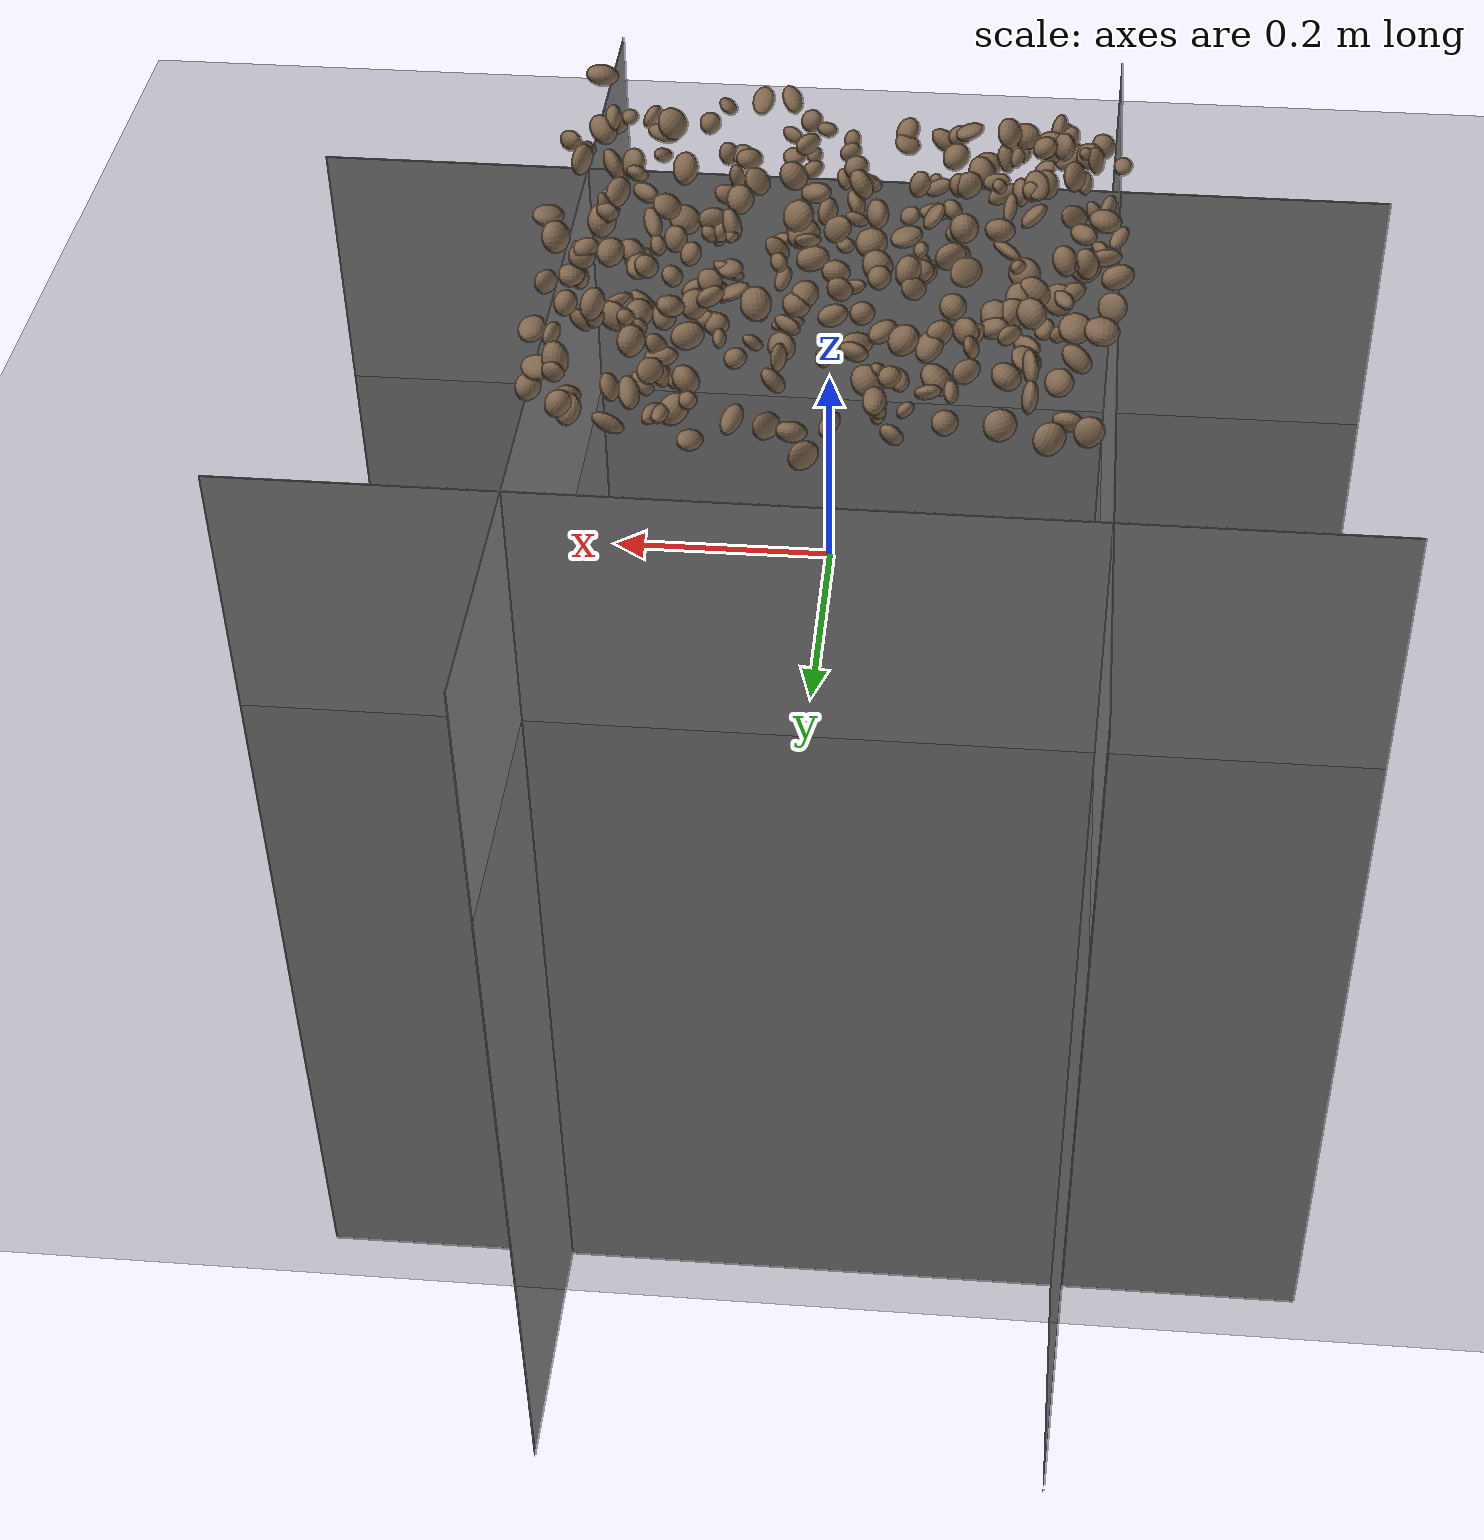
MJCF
<mujoco model="rocky_terrain_scene">

  <default>
    <default class="wall">
      <geom type="plane" size=".5 .5 .05" />
    </default>
  </default>

    <compiler angle="radian" inertiafromgeom="true" />
    <option timestep="0.002" gravity="0 0 -9.81" />

    <worldbody>

        <geom name="+x" class="wall" zaxis="1 0 0" pos="-.25 0 -.25" />
        <geom name="-x" class="wall" zaxis="-1 0 0" pos=".25 0 -.25" />
        <geom name="+y" class="wall" zaxis="0 1 0" pos="0 -.25 -.25" />
        <geom name="-y" class="wall" zaxis="0 -1 0" pos="0 .25 -.25" />

        <light name="sunlight" pos="5 5 5" dir="-1 -1 -1" diffuse="1 1 1" specular="0.5 0.5 0.5" ambient="0.5 0.5 0.5" />

        <geom name="ground_plane" type="plane" size="50 50 0.1" rgba="0.3 0.3 0.3 1" />

        <body name="rocky_terrain_body">

        </body>
    <body name="rock1" pos="0.16033222467743463 0.11732511271945328 0.3353076872749971"><joint type="free" /><geom type="ellipsoid" size="0.007908692580511224 0.006857009192502598 0.007239209682086778" quat="0.3253145827438653 0.3483351392156962 0.01907003140901329 0.3072802466314252" rgba="0.5 0.4 0.3 1" /><inertial pos="0.16033222467743463 0.11732511271945328 0.3353076872749971" quat="0.3253145827438653 0.3483351392156962 0.01907003140901329 0.3072802466314252" mass="8.846560578090317e-05" /></body><body name="rock2" pos="-0.023984638744698916 -0.1284005166196699 0.32486643466110443"><joint type="free" /><geom type="ellipsoid" size="0.008760589513443245 0.005119706609947363 0.01006578201743408" quat="0.24481590913186507 0.3521736682854592 0.051363108101960014 0.3516473144807157" rgba="0.5 0.4 0.3 1" /><inertial pos="-0.023984638744698916 -0.1284005166196699 0.32486643466110443" quat="0.24481590913186507 0.3521736682854592 0.051363108101960014 0.3516473144807157" mass="4.834450803632367e-05" /></body><body name="rock3" pos="0.1591780250956391 -0.04715970809991993 0.32300694211627273"><joint type="free" /><geom type="ellipsoid" size="0.014908029121816331 0.00643108369466274 0.007608842367872905" quat="0.2313632564795505 0.2257559265360143 0.4197012426586534 0.12317957432578179" rgba="0.5 0.4 0.3 1" /><inertial pos="0.1591780250956391 -0.04715970809991993 0.32300694211627273" quat="0.2313632564795505 0.2257559265360143 0.4197012426586534 0.12317957432578179" mass="3.617461820137646e-05" /></body><body name="rock4" pos="0.22415290772502716 -0.19880129864464746 0.322783080240883"><joint type="free" /><geom type="ellipsoid" size="0.011326026280991195 0.014743615754194285 0.011371074372675025" quat="0.06089104926489848 0.5242366766215073 0.23847891289422496 0.17639336121936935" rgba="0.5 0.4 0.3 1" /><inertial pos="0.22415290772502716 -0.19880129864464746 0.322783080240883" quat="0.06089104926489848 0.5242366766215073 0.23847891289422496 0.17639336121936935" mass="6.025459383101494e-05" /></body><body name="rock5" pos="-0.1714983208040894 -0.09668766200946866 0.31571789313658954"><joint type="free" /><geom type="ellipsoid" size="0.011777993102333618 0.006464695377488091 0.013808379400065074" quat="0.017691253257748223 0.3216367172098583 0.3559400821672053 0.30473194736518816" rgba="0.5 0.4 0.3 1" /><inertial pos="-0.1714983208040894 -0.09668766200946866 0.31571789313658954" quat="0.017691253257748223 0.3216367172098583 0.3559400821672053 0.30473194736518816" mass="2.1629924278558677e-05" /></body><body name="rock6" pos="-0.05195021149373391 -0.2354321968178933 0.31223883528119806"><joint type="free" /><geom type="ellipsoid" size="0.013481836451347755 0.009155133783990983 0.010998215612877595" quat="0.3185673431710373 0.30987236059106105 0.3384192794169621 0.033141016820939555" rgba="0.5 0.4 0.3 1" /><inertial pos="-0.05195021149373391 -0.2354321968178933 0.31223883528119806" quat="0.3185673431710373 0.30987236059106105 0.3384192794169621 0.033141016820939555" mass="9.79431859358849e-05" /></body><body name="rock7" pos="0.10687941689836788 0.08448204803219078 0.329167384153001"><joint type="free" /><geom type="ellipsoid" size="0.013218346418344594 0.012074256394564675 0.01017362397289009" quat="0.2785045091067318 0.3839238321342639 0.27254269606354975 0.0650289626954546" rgba="0.5 0.4 0.3 1" /><inertial pos="0.10687941689836788 0.08448204803219078 0.329167384153001" quat="0.2785045091067318 0.3839238321342639 0.27254269606354975 0.0650289626954546" mass="4.1246228552891115e-05" /></body><body name="rock8" pos="-0.2140811879251131 0.1048010376178033 0.3065231495975941"><joint type="free" /><geom type="ellipsoid" size="0.00800888512083414 0.014708130078061384 0.00935067392909927" quat="0.04890497004706435 0.3793010032257102 0.3404072814809291 0.23138674524629638" rgba="0.5 0.4 0.3 1" /><inertial pos="-0.2140811879251131 0.1048010376178033 0.3065231495975941" quat="0.04890497004706435 0.3793010032257102 0.3404072814809291 0.23138674524629638" mass="3.599165177455122e-05" /></body><body name="rock9" pos="0.0259470554905184 0.11225950058604311 0.3329637841746286"><joint type="free" /><geom type="ellipsoid" size="0.013872353360458004 0.005388263470425711 0.013293899290069387" quat="0.06646798245894961 0.19142233053393276 0.30384814035053065 0.4382615466565869" rgba="0.5 0.4 0.3 1" /><inertial pos="0.0259470554905184 0.11225950058604311 0.3329637841746286" quat="0.06646798245894961 0.19142233053393276 0.30384814035053065 0.4382615466565869" mass="9.365005720281411e-05" /></body><body name="rock10" pos="-0.17604775307320703 0.1375527223228335 0.31898081680825324"><joint type="free" /><geom type="ellipsoid" size="0.011002393979348601 0.01465822104459356 0.005674727370831294" quat="0.06528245859743279 0.34282015762968887 0.16942964027268423 0.4224677435001941" rgba="0.5 0.4 0.3 1" /><inertial pos="-0.17604775307320703 0.1375527223228335 0.31898081680825324" quat="0.06528245859743279 0.34282015762968887 0.16942964027268423 0.4224677435001941" mass="9.126209322396955e-05" /></body><body name="rock11" pos="-0.13731863384467863 -0.12257207610450604 0.33238140255289195"><joint type="free" /><geom type="ellipsoid" size="0.012052387094276846 0.0077336129895872715 0.005098788524126675" quat="0.35241137823491164 0.5686457752772857 0.06596677000217488 0.012976076485627807" rgba="0.5 0.4 0.3 1" /><inertial pos="-0.13731863384467863 -0.12257207610450604 0.33238140255289195" quat="0.35241137823491164 0.5686457752772857 0.06596677000217488 0.012976076485627807" mass="1.230817899345682e-05" /></body><body name="rock12" pos="-0.11353016380456993 0.19392528972400863 0.33034862342821153"><joint type="free" /><geom type="ellipsoid" size="0.006997840804560441 0.010659957115964442 0.005738731821166898" quat="0.06062412679229172 0.45065747528769184 0.08003036135157486 0.4086880365684415" rgba="0.5 0.4 0.3 1" /><inertial pos="-0.11353016380456993 0.19392528972400863 0.33034862342821153" quat="0.06062412679229172 0.45065747528769184 0.08003036135157486 0.4086880365684415" mass="6.0569472354743755e-05" /></body><body name="rock13" pos="0.1145342989028224 -0.2481339456315897 0.3233213554331312"><joint type="free" /><geom type="ellipsoid" size="0.011404671570387869 0.005375910815189248 0.009181586480216995" quat="0.3119858350652807 0.2003277614490968 0.1411019057467316 0.34658449773889094" rgba="0.5 0.4 0.3 1" /><inertial pos="0.1145342989028224 -0.2481339456315897 0.3233213554331312" quat="0.3119858350652807 0.2003277614490968 0.1411019057467316 0.34658449773889094" mass="3.291240309105297e-05" /></body><body name="rock14" pos="-0.24701565490181765 -0.07994323716003493 0.3076649657896641"><joint type="free" /><geom type="ellipsoid" size="0.012550667107689668 0.005098855001950214 0.006701338941081415" quat="0.34248448466260245 0.28128731716620675 0.24648567336134955 0.1297425248098412" rgba="0.5 0.4 0.3 1" /><inertial pos="-0.24701565490181765 -0.07994323716003493 0.3076649657896641" quat="0.34248448466260245 0.28128731716620675 0.24648567336134955 0.1297425248098412" mass="5.042994876056065e-05" /></body><body name="rock15" pos="0.025037525574296005 0.1240319964224621 0.3397769301453873"><joint type="free" /><geom type="ellipsoid" size="0.011850364553914385 0.00735422305242967 0.005842635263972322" quat="0.14015926511957624 0.04799980027515487 0.4539135450048824 0.35792738960038656" rgba="0.5 0.4 0.3 1" /><inertial pos="0.025037525574296005 0.1240319964224621 0.3397769301453873" quat="0.14015926511957624 0.04799980027515487 0.4539135450048824 0.35792738960038656" mass="2.6834589311402622e-05" /></body><body name="rock16" pos="0.12868187669648035 0.16201130403687186 0.3395868018036339"><joint type="free" /><geom type="ellipsoid" size="0.007857380008141027 0.012114763070728729 0.006344957614500655" quat="0.3531787541184363 0.3556736640238738 0.24546159748678056 0.04568598437090946" rgba="0.5 0.4 0.3 1" /><inertial pos="0.12868187669648035 0.16201130403687186 0.3395868018036339" quat="0.3531787541184363 0.3556736640238738 0.24546159748678056 0.04568598437090946" mass="1.0626719242811604e-05" /></body><body name="rock17" pos="0.09779105247794506 -0.08809419173167876 0.3292475288080158"><joint type="free" /><geom type="ellipsoid" size="0.0075817217808187174 0.00859233601543858 0.011691722479511443" quat="0.20158458850549807 0.20943889302439184 0.19192583527310134 0.39705068319700876" rgba="0.5 0.4 0.3 1" /><inertial pos="0.09779105247794506 -0.08809419173167876 0.3292475288080158" quat="0.20158458850549807 0.20943889302439184 0.19192583527310134 0.39705068319700876" mass="3.611382550850966e-05" /></body><body name="rock18" pos="0.20456463641001882 0.21952757983593102 0.349531497078986"><joint type="free" /><geom type="ellipsoid" size="0.010996493806887449 0.005928626029659573 0.009147694811156973" quat="0.13098745900530856 0.2659734828895314 0.030249023231336627 0.5727900348738234" rgba="0.5 0.4 0.3 1" /><inertial pos="0.20456463641001882 0.21952757983593102 0.349531497078986" quat="0.13098745900530856 0.2659734828895314 0.030249023231336627 0.5727900348738234" mass="8.081962857142394e-05" /></body><body name="rock19" pos="0.1072000742024593 -0.0327296634135969 0.3238139443782801"><joint type="free" /><geom type="ellipsoid" size="0.006652065551812276 0.008356527563181273 0.0069057595353997836" quat="0.2628165011841829 0.3589461568261366 0.34957802935782484 0.028659312631855585" rgba="0.5 0.4 0.3 1" /><inertial pos="0.1072000742024593 -0.0327296634135969 0.3238139443782801" quat="0.2628165011841829 0.3589461568261366 0.34957802935782484 0.028659312631855585" mass="6.049453328414143e-05" /></body><body name="rock20" pos="0.23555172613599695 0.005793743769443249 0.3380559136426831"><joint type="free" /><geom type="ellipsoid" size="0.013544276155400582 0.011404684652022365 0.01368263668364953" quat="0.5397734155594802 0.08987954688136507 0.007379685833316596 0.3629673517258381" rgba="0.5 0.4 0.3 1" /><inertial pos="0.23555172613599695 0.005793743769443249 0.3380559136426831" quat="0.5397734155594802 0.08987954688136507 0.007379685833316596 0.3629673517258381" mass="9.991447781398127e-05" /></body><body name="rock21" pos="-0.16058103565273785 -0.19856759244994382 0.33486519267738524"><joint type="free" /><geom type="ellipsoid" size="0.011424474430425168 0.011372830110481156 0.012907845805073342" quat="0.45814624463432724 0.08573616869857377 0.3563186254179538 0.09979896124914513" rgba="0.5 0.4 0.3 1" /><inertial pos="-0.16058103565273785 -0.19856759244994382 0.33486519267738524" quat="0.45814624463432724 0.08573616869857377 0.3563186254179538 0.09979896124914513" mass="2.078024292884407e-05" /></body><body name="rock22" pos="0.21001271527008053 -0.08122497768141584 0.3008755191756922"><joint type="free" /><geom type="ellipsoid" size="0.014580546005870044 0.014987709005744261 0.01245593382625346" quat="0.2547946335990302 0.23187200541801983 0.25137471541079903 0.2619586455721509" rgba="0.5 0.4 0.3 1" /><inertial pos="0.21001271527008053 -0.08122497768141584 0.3008755191756922" quat="0.2547946335990302 0.23187200541801983 0.25137471541079903 0.2619586455721509" mass="3.9095005476663005e-05" /></body><body name="rock23" pos="-0.17448026113618997 0.07911429534212489 0.33169344286027014"><joint type="free" /><geom type="ellipsoid" size="0.010233501943459419 0.012606632405885446 0.01331366767446274" quat="0.3847279602023633 0.30047807630946965 0.056506943980111204 0.2582870195080559" rgba="0.5 0.4 0.3 1" /><inertial pos="-0.17448026113618997 0.07911429534212489 0.33169344286027014" quat="0.3847279602023633 0.30047807630946965 0.056506943980111204 0.2582870195080559" mass="6.0446997564911e-05" /></body><body name="rock24" pos="0.20023410663199326 0.23059175432987883 0.3269102293623941"><joint type="free" /><geom type="ellipsoid" size="0.010388257384468282 0.01014333173682513 0.012491270711429766" quat="0.1261854827554889 0.4306836991028035 0.32935230026924267 0.11377851787246497" rgba="0.5 0.4 0.3 1" /><inertial pos="0.20023410663199326 0.23059175432987883 0.3269102293623941" quat="0.1261854827554889 0.4306836991028035 0.32935230026924267 0.11377851787246497" mass="4.813246302001149e-05" /></body><body name="rock25" pos="0.09244931308362048 0.2481655736285896 0.34881470622882654"><joint type="free" /><geom type="ellipsoid" size="0.00728923768775512 0.007006325637233552 0.007594698025107122" quat="0.44424191736014634 0.4293018432454326 0.11623131931859525 0.010224920075825946" rgba="0.5 0.4 0.3 1" /><inertial pos="0.09244931308362048 0.2481655736285896 0.34881470622882654" quat="0.44424191736014634 0.4293018432454326 0.11623131931859525 0.010224920075825946" mass="7.931933337344563e-05" /></body><body name="rock26" pos="-0.12323451886657194 -0.14577477258818655 0.327168038691753"><joint type="free" /><geom type="ellipsoid" size="0.011322278830732361 0.014454396268717765 0.011407264350398662" quat="0.11036207023060933 0.30863271980089785 0.2540413237222525 0.32696388624624023" rgba="0.5 0.4 0.3 1" /><inertial pos="-0.12323451886657194 -0.14577477258818655 0.327168038691753" quat="0.11036207023060933 0.30863271980089785 0.2540413237222525 0.32696388624624023" mass="6.934159584155304e-05" /></body><body name="rock27" pos="-0.16098575059665043 0.03376355389021918 0.34736649051047613"><joint type="free" /><geom type="ellipsoid" size="0.005480250673821017 0.010306327833983464 0.006088795983708176" quat="0.23021629308595923 0.11223096894809197 0.5751959549347467 0.082356783031202" rgba="0.5 0.4 0.3 1" /><inertial pos="-0.16098575059665043 0.03376355389021918 0.34736649051047613" quat="0.23021629308595923 0.11223096894809197 0.5751959549347467 0.082356783031202" mass="8.877428900033885e-05" /></body><body name="rock28" pos="-0.150313066078183 -0.013714536650103082 0.33259466505508684"><joint type="free" /><geom type="ellipsoid" size="0.01488616949199446 0.00534204889693236 0.007903654840511327" quat="0.20579667525800932 0.034493655416796776 0.2502217681133862 0.5094879012118076" rgba="0.5 0.4 0.3 1" /><inertial pos="-0.150313066078183 -0.013714536650103082 0.33259466505508684" quat="0.20579667525800932 0.034493655416796776 0.2502217681133862 0.5094879012118076" mass="3.871409505277248e-05" /></body><body name="rock29" pos="0.07484620288249627 0.07385172622592684 0.3362157252967564"><joint type="free" /><geom type="ellipsoid" size="0.012126688450096285 0.013524454538106856 0.005072475948411369" quat="0.44801265822042524 0.11434263511953298 0.07146526663332 0.36617944002672187" rgba="0.5 0.4 0.3 1" /><inertial pos="0.07484620288249627 0.07385172622592684 0.3362157252967564" quat="0.44801265822042524 0.11434263511953298 0.07146526663332 0.36617944002672187" mass="5.3166961984148236e-05" /></body><body name="rock30" pos="0.19709100635028237 -0.07748528123932796 0.3324463594288457"><joint type="free" /><geom type="ellipsoid" size="0.006254151019356907 0.005447028402003808 0.014152443491327472" quat="0.31146256000107875 0.04972413514029567 0.4816861725843004 0.15712713227432507" rgba="0.5 0.4 0.3 1" /><inertial pos="0.19709100635028237 -0.07748528123932796 0.3324463594288457" quat="0.31146256000107875 0.04972413514029567 0.4816861725843004 0.15712713227432507" mass="7.69360146980301e-05" /></body><body name="rock31" pos="-0.02994078720896798 0.08938927773618804 0.30008909342890927"><joint type="free" /><geom type="ellipsoid" size="0.009983954305717854 0.008953061642081326 0.014879601825719166" quat="0.3452749050662404 0.018750275817898072 0.33670991200845507 0.2992649071074064" rgba="0.5 0.4 0.3 1" /><inertial pos="-0.02994078720896798 0.08938927773618804 0.30008909342890927" quat="0.3452749050662404 0.018750275817898072 0.33670991200845507 0.2992649071074064" mass="2.9482726234856838e-05" /></body><body name="rock32" pos="-0.21469193360404415 -0.17768823102230308 0.3321340505108759"><joint type="free" /><geom type="ellipsoid" size="0.005128866819614509 0.005646759355903929 0.0054354189639635" quat="0.3554764402131936 0.10041470256589989 0.1631629230555835 0.38094593416532313" rgba="0.5 0.4 0.3 1" /><inertial pos="-0.21469193360404415 -0.17768823102230308 0.3321340505108759" quat="0.3554764402131936 0.10041470256589989 0.1631629230555835 0.38094593416532313" mass="3.9769810877269944e-05" /></body><body name="rock33" pos="0.16448071803451575 0.19065629669113016 0.31669906852272367"><joint type="free" /><geom type="ellipsoid" size="0.008603188788021065 0.011698435733795429 0.005907204851177587" quat="0.19984367396777042 0.44982931993750985 0.1824772634970065 0.1678497425977133" rgba="0.5 0.4 0.3 1" /><inertial pos="0.16448071803451575 0.19065629669113016 0.31669906852272367" quat="0.19984367396777042 0.44982931993750985 0.1824772634970065 0.1678497425977133" mass="7.89817986337568e-05" /></body><body name="rock34" pos="0.04483220588811282 -0.04691158429271014 0.31234946405872815"><joint type="free" /><geom type="ellipsoid" size="0.0061556627961681515 0.009957274001016562 0.005122947708424469" quat="0.5644003146775011 0.06516791937417978 0.0776357453267713 0.2927960206215478" rgba="0.5 0.4 0.3 1" /><inertial pos="0.04483220588811282 -0.04691158429271014 0.31234946405872815" quat="0.5644003146775011 0.06516791937417978 0.0776357453267713 0.2927960206215478" mass="7.175265975325965e-05" /></body><body name="rock35" pos="-0.04533242752710287 0.048375601837210847 0.3400937563823674"><joint type="free" /><geom type="ellipsoid" size="0.010662367224129556 0.009811478240497221 0.009996326088064379" quat="0.13803284238540972 0.3055924516415877 0.34680134701930976 0.20957335895369272" rgba="0.5 0.4 0.3 1" /><inertial pos="-0.04533242752710287 0.048375601837210847 0.3400937563823674" quat="0.13803284238540972 0.3055924516415877 0.34680134701930976 0.20957335895369272" mass="3.9819186422623066e-05" /></body><body name="rock36" pos="-0.1542402753150871 -0.1546329501950744 0.33845909565367205"><joint type="free" /><geom type="ellipsoid" size="0.005773214435327694 0.005609550612143453 0.009091835795191447" quat="0.04415882423850799 0.10616299392459651 0.6886936380703322 0.16098454376656327" rgba="0.5 0.4 0.3 1" /><inertial pos="-0.1542402753150871 -0.1546329501950744 0.33845909565367205" quat="0.04415882423850799 0.10616299392459651 0.6886936380703322 0.16098454376656327" mass="7.302147471946374e-05" /></body><body name="rock37" pos="-0.05411100805351926 0.19246455318488054 0.30609266351382963"><joint type="free" /><geom type="ellipsoid" size="0.01166526884041947 0.009879390778161447 0.0050623470343946365" quat="0.20479782367619573 0.35150280343528373 0.25427589311065046 0.1894234797778701" rgba="0.5 0.4 0.3 1" /><inertial pos="-0.05411100805351926 0.19246455318488054 0.30609266351382963" quat="0.20479782367619573 0.35150280343528373 0.25427589311065046 0.1894234797778701" mass="3.5811388988043775e-05" /></body><body name="rock38" pos="0.13950433825889458 -0.045137534538933266 0.3087085237998657"><joint type="free" /><geom type="ellipsoid" size="0.008069778803447936 0.012136354648963905 0.010903020982909958" quat="0.34226050509920564 0.33556396987047127 0.08913120636388384 0.23304431866643927" rgba="0.5 0.4 0.3 1" /><inertial pos="0.13950433825889458 -0.045137534538933266 0.3087085237998657" quat="0.34226050509920564 0.33556396987047127 0.08913120636388384 0.23304431866643927" mass="9.022355656272945e-05" /></body><body name="rock39" pos="-0.10510664235975409 -0.0952839029926808 0.3445327241946745"><joint type="free" /><geom type="ellipsoid" size="0.00845939690495669 0.010978719014763612 0.00840743186264409" quat="0.3163023624886993 0.2749472446030633 0.2323896639695733 0.17636072893866414" rgba="0.5 0.4 0.3 1" /><inertial pos="-0.10510664235975409 -0.0952839029926808 0.3445327241946745" quat="0.3163023624886993 0.2749472446030633 0.2323896639695733 0.17636072893866414" mass="3.664342753094091e-05" /></body><body name="rock40" pos="0.10660763470959445 0.1353662836525092 0.33212254326251067"><joint type="free" /><geom type="ellipsoid" size="0.009903087541831296 0.0115028882483256 0.014042736373711392" quat="0.15876798357749666 0.24528164978064088 0.2847844674456073 0.3111658991962552" rgba="0.5 0.4 0.3 1" /><inertial pos="0.10660763470959445 0.1353662836525092 0.33212254326251067" quat="0.15876798357749666 0.24528164978064088 0.2847844674456073 0.3111658991962552" mass="8.488381116895039e-05" /></body><body name="rock41" pos="-0.1699288548548843 -0.0935529512103413 0.34361632198259334"><joint type="free" /><geom type="ellipsoid" size="0.009224070462020856 0.009355288610568509 0.00997623832630527" quat="0.04179616924495063 0.10975718019335234 0.411169643747134 0.4372770068145631" rgba="0.5 0.4 0.3 1" /><inertial pos="-0.1699288548548843 -0.0935529512103413 0.34361632198259334" quat="0.04179616924495063 0.10975718019335234 0.411169643747134 0.4372770068145631" mass="5.511031115804612e-05" /></body><body name="rock42" pos="-0.017316732040218552 0.21908856725002818 0.3106938705796432"><joint type="free" /><geom type="ellipsoid" size="0.013347887397594568 0.006481447510902721 0.007299913044414155" quat="0.49687719468430913 0.08659858951244225 0.10534749459773254 0.3111767212055161" rgba="0.5 0.4 0.3 1" /><inertial pos="-0.017316732040218552 0.21908856725002818 0.3106938705796432" quat="0.49687719468430913 0.08659858951244225 0.10534749459773254 0.3111767212055161" mass="4.275945715080827e-05" /></body><body name="rock43" pos="-0.10775029851152212 0.04202539965802332 0.31008365506234337"><joint type="free" /><geom type="ellipsoid" size="0.009620393670325973 0.011351245431398005 0.011096407367081534" quat="0.011156439784891102 0.40494456351561403 0.3135073409561272 0.27039165574336776" rgba="0.5 0.4 0.3 1" /><inertial pos="-0.10775029851152212 0.04202539965802332 0.31008365506234337" quat="0.011156439784891102 0.40494456351561403 0.3135073409561272 0.27039165574336776" mass="8.90365909299936e-05" /></body><body name="rock44" pos="0.018215402928886737 -0.03181795681844346 0.30349580284328626"><joint type="free" /><geom type="ellipsoid" size="0.009660799488056229 0.010949065204768306 0.014414755619876561" quat="0.18536889516068886 0.30372289967601435 0.2714741756567111 0.23943402950658565" rgba="0.5 0.4 0.3 1" /><inertial pos="0.018215402928886737 -0.03181795681844346 0.30349580284328626" quat="0.18536889516068886 0.30372289967601435 0.2714741756567111 0.23943402950658565" mass="8.193113432828008e-05" /></body><body name="rock45" pos="-0.2072873531184395 0.012629456279646956 0.3099870426304678"><joint type="free" /><geom type="ellipsoid" size="0.008341904423147474 0.0072131801142991565 0.013283344439092334" quat="0.22902290757248828 0.10572821183615155 0.3857308095706618 0.27951807102069826" rgba="0.5 0.4 0.3 1" /><inertial pos="-0.2072873531184395 0.012629456279646956 0.3099870426304678" quat="0.22902290757248828 0.10572821183615155 0.3857308095706618 0.27951807102069826" mass="8.489341344007282e-05" /></body><body name="rock46" pos="0.1368617807674281 0.19385178939932618 0.32390234824010833"><joint type="free" /><geom type="ellipsoid" size="0.008884829221452822 0.011589351519180235 0.00694262826888119" quat="0.0029365036231274815 0.45640929039722655 0.26565295658479815 0.27500124939484777" rgba="0.5 0.4 0.3 1" /><inertial pos="0.1368617807674281 0.19385178939932618 0.32390234824010833" quat="0.0029365036231274815 0.45640929039722655 0.26565295658479815 0.27500124939484777" mass="8.72855784353347e-05" /></body><body name="rock47" pos="0.10715831950819094 -0.18100285017161766 0.31385570287528725"><joint type="free" /><geom type="ellipsoid" size="0.008418945927768004 0.011328071896809212 0.008860404714221828" quat="0.10275177795318716 0.13362634121986475 0.43271941498810135 0.3309024658388468" rgba="0.5 0.4 0.3 1" /><inertial pos="0.10715831950819094 -0.18100285017161766 0.31385570287528725" quat="0.10275177795318716 0.13362634121986475 0.43271941498810135 0.3309024658388468" mass="9.417901063525367e-05" /></body><body name="rock48" pos="-0.08198068103251066 -0.01526901243820944 0.3040954609283991"><joint type="free" /><geom type="ellipsoid" size="0.008115463890438348 0.014826986053643808 0.0073008700600696985" quat="0.3238241269820387 0.05569551554032897 0.3548816515835228 0.2655987058941095" rgba="0.5 0.4 0.3 1" /><inertial pos="-0.08198068103251066 -0.01526901243820944 0.3040954609283991" quat="0.3238241269820387 0.05569551554032897 0.3548816515835228 0.2655987058941095" mass="4.3285724007338534e-05" /></body><body name="rock49" pos="-0.20109638430796095 0.03003497859973292 0.31417481512506223"><joint type="free" /><geom type="ellipsoid" size="0.011677011355945512 0.005280313805734039 0.006820804329315636" quat="0.16425357006707084 0.19213618339400537 0.3743753781370427 0.2692348684018811" rgba="0.5 0.4 0.3 1" /><inertial pos="-0.20109638430796095 0.03003497859973292 0.31417481512506223" quat="0.16425357006707084 0.19213618339400537 0.3743753781370427 0.2692348684018811" mass="5.228186387307803e-05" /></body><body name="rock50" pos="-0.026575307674018833 -0.12558173920764343 0.3236898795657609"><joint type="free" /><geom type="ellipsoid" size="0.006813116308790956 0.006145691730102815 0.009098181985702294" quat="0.4853724890981219 0.15075614507006563 0.29548553013042783 0.06838583570138461" rgba="0.5 0.4 0.3 1" /><inertial pos="-0.026575307674018833 -0.12558173920764343 0.3236898795657609" quat="0.4853724890981219 0.15075614507006563 0.29548553013042783 0.06838583570138461" mass="4.33950090272846e-05" /></body><body name="rock51" pos="-0.14387718079062556 -0.19659994847098172 0.31158257724482186"><joint type="free" /><geom type="ellipsoid" size="0.007556728527688926 0.013208460363116698 0.007885984531013092" quat="0.06370113649686743 0.17610871519103355 0.3676049096118368 0.3925852387002622" rgba="0.5 0.4 0.3 1" /><inertial pos="-0.14387718079062556 -0.19659994847098172 0.31158257724482186" quat="0.06370113649686743 0.17610871519103355 0.3676049096118368 0.3925852387002622" mass="9.527665335837681e-05" /></body><body name="rock52" pos="0.031374017288885114 -0.20676748350692037 0.3008489662728626"><joint type="free" /><geom type="ellipsoid" size="0.006675420626076531 0.008079011712547834 0.007344600586925575" quat="0.09303433016168723 0.24368302806593445 0.185298478458075 0.4779841633143033" rgba="0.5 0.4 0.3 1" /><inertial pos="0.031374017288885114 -0.20676748350692037 0.3008489662728626" quat="0.09303433016168723 0.24368302806593445 0.185298478458075 0.4779841633143033" mass="1.2436930870061066e-05" /></body><body name="rock53" pos="0.054985837973153484 0.08797386111283512 0.3346820992883524"><joint type="free" /><geom type="ellipsoid" size="0.014394979951384508 0.011293572122722598 0.012964502310615043" quat="0.3758907727447689 0.06720765731286697 0.40443880404539173 0.15246276589697239" rgba="0.5 0.4 0.3 1" /><inertial pos="0.054985837973153484 0.08797386111283512 0.3346820992883524" quat="0.3758907727447689 0.06720765731286697 0.40443880404539173 0.15246276589697239" mass="7.046728383945918e-05" /></body><body name="rock54" pos="-0.21854020840455807 -0.03137825817561768 0.3084985771126457"><joint type="free" /><geom type="ellipsoid" size="0.012549807204778968 0.014145688478783083 0.01350849737944981" quat="0.24269823887320796 0.21618496729749642 0.11298030125163941 0.42813649257765624" rgba="0.5 0.4 0.3 1" /><inertial pos="-0.21854020840455807 -0.03137825817561768 0.3084985771126457" quat="0.24269823887320796 0.21618496729749642 0.11298030125163941 0.42813649257765624" mass="9.134304758209372e-05" /></body><body name="rock55" pos="0.20052057283933605 -0.058698011600302025 0.32469792198325376"><joint type="free" /><geom type="ellipsoid" size="0.010558126207579397 0.008549270145342507 0.007011041949803421" quat="0.05757007499605915 0.1047028898204338 0.4998246795844509 0.3379023555990561" rgba="0.5 0.4 0.3 1" /><inertial pos="0.20052057283933605 -0.058698011600302025 0.32469792198325376" quat="0.05757007499605915 0.1047028898204338 0.4998246795844509 0.3379023555990561" mass="6.672802718877614e-05" /></body><body name="rock56" pos="-0.23274300148659455 0.11608662294889366 0.3423037540101543"><joint type="free" /><geom type="ellipsoid" size="0.010348418281815965 0.013736972180366566 0.014445074826246448" quat="0.025254345674374047 0.44820018089706803 0.023953117471772086 0.5025923559567859" rgba="0.5 0.4 0.3 1" /><inertial pos="-0.23274300148659455 0.11608662294889366 0.3423037540101543" quat="0.025254345674374047 0.44820018089706803 0.023953117471772086 0.5025923559567859" mass="2.4285062003700943e-05" /></body><body name="rock57" pos="0.15895546089848606 0.24036055789884786 0.31714576060551714"><joint type="free" /><geom type="ellipsoid" size="0.00735508820360745 0.0057831830563048955 0.0142183264416911" quat="0.01219632114002235 0.33568980923388986 0.03705161939573981 0.6150622502303481" rgba="0.5 0.4 0.3 1" /><inertial pos="0.15895546089848606 0.24036055789884786 0.31714576060551714" quat="0.01219632114002235 0.33568980923388986 0.03705161939573981 0.6150622502303481" mass="8.271605766296052e-05" /></body><body name="rock58" pos="0.2354473588577985 0.13782153238847145 0.33361846165748493"><joint type="free" /><geom type="ellipsoid" size="0.01361083894809623 0.007253278281781252 0.011418697565444409" quat="0.27975205383697843 0.24832546434026903 0.2757590306342523 0.1961634511885003" rgba="0.5 0.4 0.3 1" /><inertial pos="0.2354473588577985 0.13782153238847145 0.33361846165748493" quat="0.27975205383697843 0.24832546434026903 0.2757590306342523 0.1961634511885003" mass="5.6582821987670714e-05" /></body><body name="rock59" pos="-0.04210846966783427 0.02398589593479883 0.3356181480526874"><joint type="free" /><geom type="ellipsoid" size="0.013103563714399979 0.0139889805938368 0.012366170557710374" quat="0.10248171344036608 0.23441970163662407 0.37918309677997764 0.2839154881430322" rgba="0.5 0.4 0.3 1" /><inertial pos="-0.04210846966783427 0.02398589593479883 0.3356181480526874" quat="0.10248171344036608 0.23441970163662407 0.37918309677997764 0.2839154881430322" mass="2.942279404980766e-05" /></body><body name="rock60" pos="-0.23020248372007668 -0.04368444129243926 0.31925050046924486"><joint type="free" /><geom type="ellipsoid" size="0.012866819908282714 0.005508022488885611 0.0056688361244359425" quat="0.1840802337297001 0.22994103038538022 0.23522787081845656 0.35075086506646314" rgba="0.5 0.4 0.3 1" /><inertial pos="-0.23020248372007668 -0.04368444129243926 0.31925050046924486" quat="0.1840802337297001 0.22994103038538022 0.23522787081845656 0.35075086506646314" mass="7.186014003288193e-05" /></body><body name="rock61" pos="-0.20490899800784068 0.022021727074135466 0.3453102575720607"><joint type="free" /><geom type="ellipsoid" size="0.008025048732060492 0.007183423386915851 0.00856309402923037" quat="0.4473799467231904 0.11882163837323775 0.13098136687168246 0.30281704803188936" rgba="0.5 0.4 0.3 1" /><inertial pos="-0.20490899800784068 0.022021727074135466 0.3453102575720607" quat="0.4473799467231904 0.11882163837323775 0.13098136687168246 0.30281704803188936" mass="4.54897830242335e-05" /></body><body name="rock62" pos="-0.14025713064499135 -0.10353028503525041 0.3400294555544732"><joint type="free" /><geom type="ellipsoid" size="0.006477727050304326 0.006789780774419438 0.005549966548424102" quat="0.21543765263148687 0.2912291242401063 0.3689938510679215 0.12433937206048534" rgba="0.5 0.4 0.3 1" /><inertial pos="-0.14025713064499135 -0.10353028503525041 0.3400294555544732" quat="0.21543765263148687 0.2912291242401063 0.3689938510679215 0.12433937206048534" mass="5.394648589518583e-05" /></body><body name="rock63" pos="0.01149410097367376 -0.11053424649513588 0.3020198755854858"><joint type="free" /><geom type="ellipsoid" size="0.012371901789706733 0.012419391623188508 0.008159331328177928" quat="0.3059751060105478 0.2484657375303571 0.2397262687662889 0.20583288769280622" rgba="0.5 0.4 0.3 1" /><inertial pos="0.01149410097367376 -0.11053424649513588 0.3020198755854858" quat="0.3059751060105478 0.2484657375303571 0.2397262687662889 0.20583288769280622" mass="6.660684492141759e-05" /></body><body name="rock64" pos="0.1902648667659646 0.10048049418385319 0.32405262114608663"><joint type="free" /><geom type="ellipsoid" size="0.007926551748479012 0.009678501232052942 0.010401400075385883" quat="0.5483930134271979 0.13880440434236843 0.02938132745213584 0.2834212547782978" rgba="0.5 0.4 0.3 1" /><inertial pos="0.1902648667659646 0.10048049418385319 0.32405262114608663" quat="0.5483930134271979 0.13880440434236843 0.02938132745213584 0.2834212547782978" mass="6.905592656129463e-05" /></body><body name="rock65" pos="-0.2152237083765814 -0.030397675064720298 0.3410955582362134"><joint type="free" /><geom type="ellipsoid" size="0.009283993293344797 0.007868619807528808 0.013632550566973597" quat="0.35654480432479363 0.37879351953195367 0.15683302302241306 0.1078286531208397" rgba="0.5 0.4 0.3 1" /><inertial pos="-0.2152237083765814 -0.030397675064720298 0.3410955582362134" quat="0.35654480432479363 0.37879351953195367 0.15683302302241306 0.1078286531208397" mass="5.0603200538454206e-05" /></body><body name="rock66" pos="-0.16621040134741966 -0.02858028151676173 0.3005649172836731"><joint type="free" /><geom type="ellipsoid" size="0.01005035810438877 0.014475178955044403 0.013215811438059902" quat="0.0198607963570304 0.47844683808177774 0.31331989186472264 0.18837247369646928" rgba="0.5 0.4 0.3 1" /><inertial pos="-0.16621040134741966 -0.02858028151676173 0.3005649172836731" quat="0.0198607963570304 0.47844683808177774 0.31331989186472264 0.18837247369646928" mass="4.06955753529932e-05" /></body><body name="rock67" pos="0.01819747671892874 0.011730685219079828 0.3497116700291154"><joint type="free" /><geom type="ellipsoid" size="0.010757070857659371 0.005294066077982173 0.01232982203116532" quat="0.02630538402209402 0.1680709708512042 0.24864725627062315 0.5569763888560787" rgba="0.5 0.4 0.3 1" /><inertial pos="0.01819747671892874 0.011730685219079828 0.3497116700291154" quat="0.02630538402209402 0.1680709708512042 0.24864725627062315 0.5569763888560787" mass="3.1633438757218214e-05" /></body><body name="rock68" pos="0.08808476535640641 0.05348242938532388 0.32170263469752153"><joint type="free" /><geom type="ellipsoid" size="0.008411828457275021 0.014596465611410647 0.005900583940664371" quat="0.32739910977944425 0.19313817470118552 0.3530482139158081 0.12641450160356216" rgba="0.5 0.4 0.3 1" /><inertial pos="0.08808476535640641 0.05348242938532388 0.32170263469752153" quat="0.32739910977944425 0.19313817470118552 0.3530482139158081 0.12641450160356216" mass="9.350319749679433e-05" /></body><body name="rock69" pos="-0.11787825532344881 0.04843725850624525 0.3494385405705172"><joint type="free" /><geom type="ellipsoid" size="0.011973659388723447 0.005150864819219459 0.014737013509494322" quat="0.30719869285646634 0.0033713912968304604 0.44045757336829394 0.24897234247840933" rgba="0.5 0.4 0.3 1" /><inertial pos="-0.11787825532344881 0.04843725850624525 0.3494385405705172" quat="0.30719869285646634 0.0033713912968304604 0.44045757336829394 0.24897234247840933" mass="1.3011129707421666e-05" /></body><body name="rock70" pos="0.13509204027085003 0.01427345908480876 0.3095115730499648"><joint type="free" /><geom type="ellipsoid" size="0.00983523570843501 0.008120506804073932 0.009442692218546614" quat="0.35566574017240404 0.18148030186911865 0.0996968851644313 0.3631570727940461" rgba="0.5 0.4 0.3 1" /><inertial pos="0.13509204027085003 0.01427345908480876 0.3095115730499648" quat="0.35566574017240404 0.18148030186911865 0.0996968851644313 0.3631570727940461" mass="3.287016949848993e-05" /></body><body name="rock71" pos="-0.23390290207756975 -0.0708354151560141 0.32997128475866433"><joint type="free" /><geom type="ellipsoid" size="0.013781357958998253 0.009730261753345059 0.013989102955041587" quat="0.19239668659847778 0.1838550118529376 0.25321930209557963 0.370528999453005" rgba="0.5 0.4 0.3 1" /><inertial pos="-0.23390290207756975 -0.0708354151560141 0.32997128475866433" quat="0.19239668659847778 0.1838550118529376 0.25321930209557963 0.370528999453005" mass="7.147558437389003e-05" /></body><body name="rock72" pos="-0.033103284630600194 -0.031168957393338748 0.32263398834525586"><joint type="free" /><geom type="ellipsoid" size="0.013401017271305483 0.012399512943459381 0.013681594564795653" quat="0.20602767431082175 0.2461780165639203 0.3339224060963915 0.2138719030288665" rgba="0.5 0.4 0.3 1" /><inertial pos="-0.033103284630600194 -0.031168957393338748 0.32263398834525586" quat="0.20602767431082175 0.2461780165639203 0.3339224060963915 0.2138719030288665" mass="5.258699205823309e-05" /></body><body name="rock73" pos="0.1713317403787037 -0.0032427285202871192 0.3209617059255616"><joint type="free" /><geom type="ellipsoid" size="0.012661739981056566 0.011878199908441203 0.009251344815073897" quat="0.1525458954885411 0.1857593514094119 0.5072171143361728 0.15447763876587417" rgba="0.5 0.4 0.3 1" /><inertial pos="0.1713317403787037 -0.0032427285202871192 0.3209617059255616" quat="0.1525458954885411 0.1857593514094119 0.5072171143361728 0.15447763876587417" mass="3.35034070157313e-05" /></body><body name="rock74" pos="0.09530018342986729 0.06929891872520166 0.342839557858027"><joint type="free" /><geom type="ellipsoid" size="0.010082738918481386 0.006617151388969542 0.010660481171785207" quat="0.5735392177125213 0.14898558387113334 0.23349227808533884 0.043982920331006564" rgba="0.5 0.4 0.3 1" /><inertial pos="0.09530018342986729 0.06929891872520166 0.342839557858027" quat="0.5735392177125213 0.14898558387113334 0.23349227808533884 0.043982920331006564" mass="5.976962818716676e-05" /></body><body name="rock75" pos="-0.07814524676992335 0.216633377230264 0.3267187736463183"><joint type="free" /><geom type="ellipsoid" size="0.007555214922712341 0.00811396514733089 0.0052399183709737965" quat="0.33591105242230757 0.2673416180133338 0.03339855416472872 0.36334877539962995" rgba="0.5 0.4 0.3 1" /><inertial pos="-0.07814524676992335 0.216633377230264 0.3267187736463183" quat="0.33591105242230757 0.2673416180133338 0.03339855416472872 0.36334877539962995" mass="2.1847911770040276e-05" /></body><body name="rock76" pos="0.15215502713136475 0.06454186221943897 0.31446616416199724"><joint type="free" /><geom type="ellipsoid" size="0.008006059726273456 0.006017742047898923 0.014559002295583011" quat="0.29234076341845083 0.2091961625262936 0.09057096054055783 0.40789211351469773" rgba="0.5 0.4 0.3 1" /><inertial pos="0.15215502713136475 0.06454186221943897 0.31446616416199724" quat="0.29234076341845083 0.2091961625262936 0.09057096054055783 0.40789211351469773" mass="8.436321402867291e-05" /></body><body name="rock77" pos="0.03388500180354359 -0.05102825664870575 0.32165540956522365"><joint type="free" /><geom type="ellipsoid" size="0.010421218816828032 0.009291610229413747 0.007554168116360935" quat="0.03314786270320353 0.2774652756265902 0.3946611619452639 0.2947256997249424" rgba="0.5 0.4 0.3 1" /><inertial pos="0.03388500180354359 -0.05102825664870575 0.32165540956522365" quat="0.03314786270320353 0.2774652756265902 0.3946611619452639 0.2947256997249424" mass="8.765327522016637e-05" /></body><body name="rock78" pos="-0.24143274018784294 0.06384846622155854 0.3313026048531595"><joint type="free" /><geom type="ellipsoid" size="0.005689416535813272 0.012792108113161928 0.012392206796747176" quat="0.3773779380633712 0.2581085498603593 0.05542195991846616 0.30909155215780343" rgba="0.5 0.4 0.3 1" /><inertial pos="-0.24143274018784294 0.06384846622155854 0.3313026048531595" quat="0.3773779380633712 0.2581085498603593 0.05542195991846616 0.30909155215780343" mass="6.316657931990418e-05" /></body><body name="rock79" pos="-0.03579138794972769 0.07979185496255409 0.3238835080183628"><joint type="free" /><geom type="ellipsoid" size="0.005873920809870881 0.005720779942322963 0.00631403541253804" quat="0.29666892471660095 0.0885607546362467 0.46517703102508734 0.14959328962206503" rgba="0.5 0.4 0.3 1" /><inertial pos="-0.03579138794972769 0.07979185496255409 0.3238835080183628" quat="0.29666892471660095 0.0885607546362467 0.46517703102508734 0.14959328962206503" mass="7.423638525543862e-05" /></body><body name="rock80" pos="-0.15691248882203362 0.15887106762638636 0.32315112187789924"><joint type="free" /><geom type="ellipsoid" size="0.010709728469927208 0.012865294654631185 0.01270009846047477" quat="0.5066190797293031 0.17229907814107034 0.31437648019230796 0.00670536193731868" rgba="0.5 0.4 0.3 1" /><inertial pos="-0.15691248882203362 0.15887106762638636 0.32315112187789924" quat="0.5066190797293031 0.17229907814107034 0.31437648019230796 0.00670536193731868" mass="1.3862945746822338e-05" /></body><body name="rock81" pos="0.021037690666155906 -0.1013992962350369 0.32645312445046454"><joint type="free" /><geom type="ellipsoid" size="0.014941194069886098 0.008535332318444472 0.010611560766896528" quat="0.04580647801610421 0.1702084824347542 0.3694098046478715 0.4145752349012701" rgba="0.5 0.4 0.3 1" /><inertial pos="0.021037690666155906 -0.1013992962350369 0.32645312445046454" quat="0.04580647801610421 0.1702084824347542 0.3694098046478715 0.4145752349012701" mass="1.1095818496394501e-05" /></body><body name="rock82" pos="0.09445768435797358 -0.1777273119499979 0.31584541072900446"><joint type="free" /><geom type="ellipsoid" size="0.012067235073785789 0.005807822143560754 0.009166019207570666" quat="0.015266782976624045 0.1592695507259363 0.5394322202140797 0.28603144608336006" rgba="0.5 0.4 0.3 1" /><inertial pos="0.09445768435797358 -0.1777273119499979 0.31584541072900446" quat="0.015266782976624045 0.1592695507259363 0.5394322202140797 0.28603144608336006" mass="3.969109932072838e-05" /></body><body name="rock83" pos="0.16618481434535753 -0.003309897703370479 0.31493601150434947"><joint type="free" /><geom type="ellipsoid" size="0.012757069634272719 0.00772040247577534 0.0086802411807875" quat="0.4538403638655985 0.3077582284283771 0.1169481666556934 0.121453241050331" rgba="0.5 0.4 0.3 1" /><inertial pos="0.16618481434535753 -0.003309897703370479 0.31493601150434947" quat="0.4538403638655985 0.3077582284283771 0.1169481666556934 0.121453241050331" mass="6.820013471055185e-05" /></body><body name="rock84" pos="-0.011142062427074828 -0.026201083670394143 0.32232963170656725"><joint type="free" /><geom type="ellipsoid" size="0.008440024621962467 0.006125483419488069 0.007868582594183025" quat="0.209111959450999 0.196436229110334 0.2540436371453036 0.3404081742933634" rgba="0.5 0.4 0.3 1" /><inertial pos="-0.011142062427074828 -0.026201083670394143 0.32232963170656725" quat="0.209111959450999 0.196436229110334 0.2540436371453036 0.3404081742933634" mass="9.312843590305236e-05" /></body><body name="rock85" pos="-0.011236510421351098 0.11071838513113513 0.3419681806763566"><joint type="free" /><geom type="ellipsoid" size="0.010182716326228785 0.008809336244491362 0.012581947970384887" quat="0.08187349515639447 0.42262633033989416 0.18258738091168358 0.3129127935920277" rgba="0.5 0.4 0.3 1" /><inertial pos="-0.011236510421351098 0.11071838513113513 0.3419681806763566" quat="0.08187349515639447 0.42262633033989416 0.18258738091168358 0.3129127935920277" mass="8.296588544396331e-05" /></body><body name="rock86" pos="0.19507130627540425 0.2177188694722541 0.3119888442845976"><joint type="free" /><geom type="ellipsoid" size="0.012113249223547751 0.013427192978901735 0.008287292888446238" quat="0.20653735972997547 0.09751694135921553 0.264849082765247 0.43109661614556205" rgba="0.5 0.4 0.3 1" /><inertial pos="0.19507130627540425 0.2177188694722541 0.3119888442845976" quat="0.20653735972997547 0.09751694135921553 0.264849082765247 0.43109661614556205" mass="3.394119647376237e-05" /></body><body name="rock87" pos="0.10826486547395553 0.09596304239845221 0.30765249775808196"><joint type="free" /><geom type="ellipsoid" size="0.010362339723431806 0.005838306402394352 0.010808903318179096" quat="0.025216959016744405 0.268136829961114 0.5397401684817538 0.1669060425403878" rgba="0.5 0.4 0.3 1" /><inertial pos="0.10826486547395553 0.09596304239845221 0.30765249775808196" quat="0.025216959016744405 0.268136829961114 0.5397401684817538 0.1669060425403878" mass="7.97393755998648e-05" /></body><body name="rock88" pos="-0.15731692477421066 0.12021763439658356 0.33726960832661795"><joint type="free" /><geom type="ellipsoid" size="0.006241980892106694 0.00953049296805509 0.011191313112801027" quat="0.2144587263196428 0.08751561829008321 0.34083270047006203 0.35719295492021197" rgba="0.5 0.4 0.3 1" /><inertial pos="-0.15731692477421066 0.12021763439658356 0.33726960832661795" quat="0.2144587263196428 0.08751561829008321 0.34083270047006203 0.35719295492021197" mass="8.830449579424533e-05" /></body><body name="rock89" pos="0.04406203364697403 -0.13663000001154862 0.3211397476777993"><joint type="free" /><geom type="ellipsoid" size="0.011540198989791127 0.011608510021044183 0.013767665996732542" quat="0.4544875145222454 0.053070484656919305 0.1676045418339345 0.32483745898690086" rgba="0.5 0.4 0.3 1" /><inertial pos="0.04406203364697403 -0.13663000001154862 0.3211397476777993" quat="0.4544875145222454 0.053070484656919305 0.1676045418339345 0.32483745898690086" mass="6.21941109174467e-05" /></body><body name="rock90" pos="-0.08851440419090306 -0.19773024282846885 0.3263586154317113"><joint type="free" /><geom type="ellipsoid" size="0.009930400208632496 0.014966845625211195 0.008724729377689786" quat="0.03528755709797361 0.3384352511368484 0.39518736500121615 0.23108982676396178" rgba="0.5 0.4 0.3 1" /><inertial pos="-0.08851440419090306 -0.19773024282846885 0.3263586154317113" quat="0.03528755709797361 0.3384352511368484 0.39518736500121615 0.23108982676396178" mass="5.482480567839673e-05" /></body><body name="rock91" pos="-0.19018450765224104 -0.22299902212489897 0.3272946678650024"><joint type="free" /><geom type="ellipsoid" size="0.014761209019638549 0.014735492513851912 0.007143078558385962" quat="0.3642343259634917 0.17005432570072587 0.3002582934839657 0.1654530548518168" rgba="0.5 0.4 0.3 1" /><inertial pos="-0.19018450765224104 -0.22299902212489897 0.3272946678650024" quat="0.3642343259634917 0.17005432570072587 0.3002582934839657 0.1654530548518168" mass="6.126787841312034e-05" /></body><body name="rock92" pos="-0.19755017880413223 -0.2473936875389785 0.31267835081436796"><joint type="free" /><geom type="ellipsoid" size="0.006624309413296833 0.007592830911457516 0.007043026507346581" quat="0.5123529338428195 0.24366582182690383 0.13921321255504548 0.10476803177523124" rgba="0.5 0.4 0.3 1" /><inertial pos="-0.19755017880413223 -0.2473936875389785 0.31267835081436796" quat="0.5123529338428195 0.24366582182690383 0.13921321255504548 0.10476803177523124" mass="6.829148679641081e-05" /></body><body name="rock93" pos="-0.16467361206383502 0.035598626264243094 0.3155818065755658"><joint type="free" /><geom type="ellipsoid" size="0.012586944146072188 0.014955998798926857 0.013568189261566808" quat="0.06411491480453964 0.19394764602278722 0.3093954349950124 0.4325420041776607" rgba="0.5 0.4 0.3 1" /><inertial pos="-0.16467361206383502 0.035598626264243094 0.3155818065755658" quat="0.06411491480453964 0.19394764602278722 0.3093954349950124 0.4325420041776607" mass="5.245114949675017e-05" /></body><body name="rock94" pos="-0.10044542392639688 -0.0786798263323753 0.3295553249932153"><joint type="free" /><geom type="ellipsoid" size="0.010092580593077893 0.009212398069893468 0.007461160334558542" quat="0.1409316952756862 0.2490104480953028 0.35449220654025715 0.2555656500887538" rgba="0.5 0.4 0.3 1" /><inertial pos="-0.10044542392639688 -0.0786798263323753 0.3295553249932153" quat="0.1409316952756862 0.2490104480953028 0.35449220654025715 0.2555656500887538" mass="2.275299241461088e-05" /></body><body name="rock95" pos="0.0632340015337493 0.20543740618657746 0.30104190095871264"><joint type="free" /><geom type="ellipsoid" size="0.0070166618151321376 0.014417680719323912 0.008086718580697977" quat="0.1530205249684348 0.31479788037928996 0.05469441962955656 0.47748717502271876" rgba="0.5 0.4 0.3 1" /><inertial pos="0.0632340015337493 0.20543740618657746 0.30104190095871264" quat="0.1530205249684348 0.31479788037928996 0.05469441962955656 0.47748717502271876" mass="3.0880154875608746e-05" /></body><body name="rock96" pos="0.05598619518770093 0.0625223325519138 0.30972965601076485"><joint type="free" /><geom type="ellipsoid" size="0.005072750596677888 0.006015108166823999 0.009451741379573383" quat="0.3359113327322534 0.18748696224434447 0.0703448802668718 0.40625682475653035" rgba="0.5 0.4 0.3 1" /><inertial pos="0.05598619518770093 0.0625223325519138 0.30972965601076485" quat="0.3359113327322534 0.18748696224434447 0.0703448802668718 0.40625682475653035" mass="4.200820647124681e-05" /></body><body name="rock97" pos="-0.016851164084759673 -0.08002226034220677 0.31500209053183803"><joint type="free" /><geom type="ellipsoid" size="0.01069501263881292 0.005178399078549264 0.005994132610661467" quat="0.08687860840184673 0.7235851023870724 0.0272597318557994 0.16227655735528143" rgba="0.5 0.4 0.3 1" /><inertial pos="-0.016851164084759673 -0.08002226034220677 0.31500209053183803" quat="0.08687860840184673 0.7235851023870724 0.0272597318557994 0.16227655735528143" mass="7.524530704643339e-05" /></body><body name="rock98" pos="0.1250143524741238 0.1629212906904351 0.3297635109323624"><joint type="free" /><geom type="ellipsoid" size="0.011316501229847271 0.00814320315202349 0.01365744624518455" quat="0.18283798558017295 0.34214785381667534 0.19448273969407104 0.2805314209090807" rgba="0.5 0.4 0.3 1" /><inertial pos="0.1250143524741238 0.1629212906904351 0.3297635109323624" quat="0.18283798558017295 0.34214785381667534 0.19448273969407104 0.2805314209090807" mass="9.702484049800401e-05" /></body><body name="rock99" pos="0.11550280371055394 0.1587651861215304 0.30301674904534454"><joint type="free" /><geom type="ellipsoid" size="0.006339380791698347 0.006454998643087333 0.005813431783664629" quat="0.2650561457583543 0.32539944313238367 0.19859987202886692 0.2109445390803951" rgba="0.5 0.4 0.3 1" /><inertial pos="0.11550280371055394 0.1587651861215304 0.30301674904534454" quat="0.2650561457583543 0.32539944313238367 0.19859987202886692 0.2109445390803951" mass="6.137306468725639e-05" /></body><body name="rock100" pos="0.10061149018212412 -0.0658055959366231 0.30333517615461525"><joint type="free" /><geom type="ellipsoid" size="0.010520313870317438 0.0069151924249561915 0.012485115560781995" quat="0.09603395526742 0.3722932305293243 0.4165440351823365 0.11512877902091923" rgba="0.5 0.4 0.3 1" /><inertial pos="0.10061149018212412 -0.0658055959366231 0.30333517615461525" quat="0.09603395526742 0.3722932305293243 0.4165440351823365 0.11512877902091923" mass="7.274233412850879e-05" /></body><body name="rock101" pos="0.03080709755876959 0.11881627381706011 0.3142469931695986"><joint type="free" /><geom type="ellipsoid" size="0.012809292540979988 0.012196773119950405 0.008743682525929622" quat="0.09530802325559475 0.14247182302844805 0.29844787928865546 0.4637722744273018" rgba="0.5 0.4 0.3 1" /><inertial pos="0.03080709755876959 0.11881627381706011 0.3142469931695986" quat="0.09530802325559475 0.14247182302844805 0.29844787928865546 0.4637722744273018" mass="5.2950094229083886e-05" /></body><body name="rock102" pos="-0.10161321377660448 -0.19462772447326732 0.33460158372782367"><joint type="free" /><geom type="ellipsoid" size="0.013917850680461943 0.009111038625984334 0.00923841387248555" quat="0.08322036685242971 0.5074369396263764 0.27179666979442463 0.13754602372676927" rgba="0.5 0.4 0.3 1" /><inertial pos="-0.10161321377660448 -0.19462772447326732 0.33460158372782367" quat="0.08322036685242971 0.5074369396263764 0.27179666979442463 0.13754602372676927" mass="4.0336592741474354e-05" /></body><body name="rock103" pos="-0.2150247209032402 -0.13877283598423318 0.325871386947557"><joint type="free" /><geom type="ellipsoid" size="0.007728972709913198 0.011055542352372383 0.006449282279196273" quat="0.14327070326681293 0.5627304503550364 0.07165032247577921 0.22234852390237142" rgba="0.5 0.4 0.3 1" /><inertial pos="-0.2150247209032402 -0.13877283598423318 0.325871386947557" quat="0.14327070326681293 0.5627304503550364 0.07165032247577921 0.22234852390237142" mass="2.155912095729392e-05" /></body><body name="rock104" pos="-0.12882356074892565 0.07986018479208912 0.3077963256762184"><joint type="free" /><geom type="ellipsoid" size="0.006038910643860203 0.01421703150482535 0.006032518146763358" quat="0.3059286895668264 0.14560932382674432 0.2728007400585216 0.2756612465479077" rgba="0.5 0.4 0.3 1" /><inertial pos="-0.12882356074892565 0.07986018479208912 0.3077963256762184" quat="0.3059286895668264 0.14560932382674432 0.2728007400585216 0.2756612465479077" mass="5.275068392856218e-05" /></body><body name="rock105" pos="-0.15573672435010638 -0.20489694169458317 0.3156745098324443"><joint type="free" /><geom type="ellipsoid" size="0.01458023722379459 0.009545884086595152 0.008331224017843933" quat="0.3482201310304879 0.030199886154777766 0.137906939284964 0.48367304352977025" rgba="0.5 0.4 0.3 1" /><inertial pos="-0.15573672435010638 -0.20489694169458317 0.3156745098324443" quat="0.3482201310304879 0.030199886154777766 0.137906939284964 0.48367304352977025" mass="3.352196493238928e-05" /></body><body name="rock106" pos="-0.18402029919756357 -0.2038836728502864 0.32171255930270937"><joint type="free" /><geom type="ellipsoid" size="0.012173562542384282 0.014984445680051094 0.014837656991351353" quat="0.36826503995264764 0.11665996875311188 0.17865917643444565 0.3364158148597948" rgba="0.5 0.4 0.3 1" /><inertial pos="-0.18402029919756357 -0.2038836728502864 0.32171255930270937" quat="0.36826503995264764 0.11665996875311188 0.17865917643444565 0.3364158148597948" mass="1.9521621732441865e-05" /></body><body name="rock107" pos="-0.03196566023783021 0.15271973605553502 0.3361321332979083"><joint type="free" /><geom type="ellipsoid" size="0.011050900397152237 0.0071204621914960475 0.013024552331047358" quat="0.2254490809384181 0.4822596157143087 0.007314992464263668 0.2849763108830095" rgba="0.5 0.4 0.3 1" /><inertial pos="-0.03196566023783021 0.15271973605553502 0.3361321332979083" quat="0.2254490809384181 0.4822596157143087 0.007314992464263668 0.2849763108830095" mass="9.65865330049368e-05" /></body><body name="rock108" pos="-0.07056718233074377 -0.1011038118333158 0.3400850431091563"><joint type="free" /><geom type="ellipsoid" size="0.00930545421448157 0.012792948598839362 0.008084633671977697" quat="0.22463814245863964 0.08427899497837774 0.34718229941723505 0.3439005631457475" rgba="0.5 0.4 0.3 1" /><inertial pos="-0.07056718233074377 -0.1011038118333158 0.3400850431091563" quat="0.22463814245863964 0.08427899497837774 0.34718229941723505 0.3439005631457475" mass="6.27517664107987e-05" /></body><body name="rock109" pos="-0.06215533721957445 -0.05359580366937805 0.31617305815692814"><joint type="free" /><geom type="ellipsoid" size="0.012592371569238429 0.014670135590934223 0.007215438051631504" quat="0.2756299569559187 0.054776556045274795 0.01684604863056914 0.6527474383682373" rgba="0.5 0.4 0.3 1" /><inertial pos="-0.06215533721957445 -0.05359580366937805 0.31617305815692814" quat="0.2756299569559187 0.054776556045274795 0.01684604863056914 0.6527474383682373" mass="8.921215142568217e-05" /></body><body name="rock110" pos="0.18656787046270978 0.12218493028511906 0.349987940875084"><joint type="free" /><geom type="ellipsoid" size="0.014034602637216703 0.01074037466528769 0.009414498855107239" quat="0.43987522772770893 0.18366740333883436 0.37569736624811706 0.0007600026853396973" rgba="0.5 0.4 0.3 1" /><inertial pos="0.18656787046270978 0.12218493028511906 0.349987940875084" quat="0.43987522772770893 0.18366740333883436 0.37569736624811706 0.0007600026853396973" mass="3.4934694199885945e-05" /></body><body name="rock111" pos="-0.012850017345749754 0.057915943402303216 0.33281941848780694"><joint type="free" /><geom type="ellipsoid" size="0.007667520428835522 0.012559892846482809 0.010241322733708046" quat="0.22683096459300575 0.267474255004238 0.3407945928250383 0.164900187577718" rgba="0.5 0.4 0.3 1" /><inertial pos="-0.012850017345749754 0.057915943402303216 0.33281941848780694" quat="0.22683096459300575 0.267474255004238 0.3407945928250383 0.164900187577718" mass="4.000095698652854e-05" /></body><body name="rock112" pos="0.053665649122148495 0.12793148668231286 0.3234700226985007"><joint type="free" /><geom type="ellipsoid" size="0.007119000609628405 0.005347535279938373 0.010068435031025592" quat="0.20763054393614477 0.13077218576579314 0.17022497129022585 0.4913722990078362" rgba="0.5 0.4 0.3 1" /><inertial pos="0.053665649122148495 0.12793148668231286 0.3234700226985007" quat="0.20763054393614477 0.13077218576579314 0.17022497129022585 0.4913722990078362" mass="3.714108693381496e-05" /></body><body name="rock113" pos="-0.09187760884987761 0.11940210771157567 0.3216380104964679"><joint type="free" /><geom type="ellipsoid" size="0.014066514389003242 0.008961297709835813 0.011588060278191472" quat="0.35112297547613947 0.299132464403947 0.3076288123205228 0.042115747799390674" rgba="0.5 0.4 0.3 1" /><inertial pos="-0.09187760884987761 0.11940210771157567 0.3216380104964679" quat="0.35112297547613947 0.299132464403947 0.3076288123205228 0.042115747799390674" mass="8.153578404653403e-05" /></body><body name="rock114" pos="-0.06510756217771602 -0.04497425581273068 0.3430654167583851"><joint type="free" /><geom type="ellipsoid" size="0.007934324246985503 0.005508562523235085 0.009435688037744739" quat="0.2752289376721043 0.266823781510977 0.4014439874509873 0.056503293365931344" rgba="0.5 0.4 0.3 1" /><inertial pos="-0.06510756217771602 -0.04497425581273068 0.3430654167583851" quat="0.2752289376721043 0.266823781510977 0.4014439874509873 0.056503293365931344" mass="6.847950944287733e-05" /></body><body name="rock115" pos="0.17159632606660769 -0.09508522877949005 0.32300848083017636"><joint type="free" /><geom type="ellipsoid" size="0.014647110335505413 0.008322316305729532 0.007464345567547006" quat="0.11535708573822022 0.1639085306841549 0.3650030385001291 0.35573134507749565" rgba="0.5 0.4 0.3 1" /><inertial pos="0.17159632606660769 -0.09508522877949005 0.32300848083017636" quat="0.11535708573822022 0.1639085306841549 0.3650030385001291 0.35573134507749565" mass="7.929200234423541e-05" /></body><body name="rock116" pos="-0.07031791121496339 0.11982523543650314 0.32722222443972704"><joint type="free" /><geom type="ellipsoid" size="0.012812611920740034 0.014162912643978138 0.011347928263722811" quat="0.34449682559805966 0.10770369546957444 0.20671144895270357 0.3410880299796624" rgba="0.5 0.4 0.3 1" /><inertial pos="-0.07031791121496339 0.11982523543650314 0.32722222443972704" quat="0.34449682559805966 0.10770369546957444 0.20671144895270357 0.3410880299796624" mass="3.168711587956071e-05" /></body><body name="rock117" pos="-0.005965262100561086 0.013727376757019794 0.32064814954907994"><joint type="free" /><geom type="ellipsoid" size="0.009795961448260606 0.012169249503952987 0.012041209405364111" quat="0.31618851858134595 0.24434756935232224 0.34351404119671003 0.09594987086962183" rgba="0.5 0.4 0.3 1" /><inertial pos="-0.005965262100561086 0.013727376757019794 0.32064814954907994" quat="0.31618851858134595 0.24434756935232224 0.34351404119671003 0.09594987086962183" mass="9.82942304778857e-05" /></body><body name="rock118" pos="0.0010905846625239302 0.24915889009099002 0.3007909614375705"><joint type="free" /><geom type="ellipsoid" size="0.006096315602168997 0.013099426628816326 0.014321295426261559" quat="0.32401618965819934 0.025382463445573798 0.09584458068622641 0.5547567662100005" rgba="0.5 0.4 0.3 1" /><inertial pos="0.0010905846625239302 0.24915889009099002 0.3007909614375705" quat="0.32401618965819934 0.025382463445573798 0.09584458068622641 0.5547567662100005" mass="3.1132418577596635e-05" /></body><body name="rock119" pos="0.08404097261437193 0.01971702293175076 0.3231130978075241"><joint type="free" /><geom type="ellipsoid" size="0.010355897677172661 0.00619836385287806 0.011080275834964744" quat="0.3352178049895243 0.3122689581522069 0.2016385701783558 0.150874666679913" rgba="0.5 0.4 0.3 1" /><inertial pos="0.08404097261437193 0.01971702293175076 0.3231130978075241" quat="0.3352178049895243 0.3122689581522069 0.2016385701783558 0.150874666679913" mass="3.507234537143198e-05" /></body><body name="rock120" pos="0.05290978912980571 -0.22668682000319224 0.34549623462563245"><joint type="free" /><geom type="ellipsoid" size="0.014400465556946053 0.007174156279964281 0.009045941316756734" quat="0.29377215559181596 0.08843282355817159 0.3148465068392506 0.3029485140107619" rgba="0.5 0.4 0.3 1" /><inertial pos="0.05290978912980571 -0.22668682000319224 0.34549623462563245" quat="0.29377215559181596 0.08843282355817159 0.3148465068392506 0.3029485140107619" mass="7.313724531269712e-05" /></body><body name="rock121" pos="-0.054348546355010185 0.22503161291586354 0.3332443508544676"><joint type="free" /><geom type="ellipsoid" size="0.006970208079644578 0.006539646097184819 0.010413216021538451" quat="0.3719473035816619 0.24453103748796942 0.13593147088491725 0.2475901880454515" rgba="0.5 0.4 0.3 1" /><inertial pos="-0.054348546355010185 0.22503161291586354 0.3332443508544676" quat="0.3719473035816619 0.24453103748796942 0.13593147088491725 0.2475901880454515" mass="3.045042041346585e-05" /></body><body name="rock122" pos="0.1339466935183144 -0.07025235414153747 0.31298063212170046"><joint type="free" /><geom type="ellipsoid" size="0.010896235284237579 0.013597264846445092 0.014396208567901171" quat="0.10027094963051736 0.34435752624355476 0.0026085853215308185 0.552762938804397" rgba="0.5 0.4 0.3 1" /><inertial pos="0.1339466935183144 -0.07025235414153747 0.31298063212170046" quat="0.10027094963051736 0.34435752624355476 0.0026085853215308185 0.552762938804397" mass="4.18564793579259e-05" /></body><body name="rock123" pos="-0.19524415176600568 -0.17700071784059368 0.3384218196465868"><joint type="free" /><geom type="ellipsoid" size="0.01283834280354966 0.01200728194703599 0.007488291585728554" quat="0.040879796363415696 0.306150033686712 0.21651172210999245 0.43645844783987986" rgba="0.5 0.4 0.3 1" /><inertial pos="-0.19524415176600568 -0.17700071784059368 0.3384218196465868" quat="0.040879796363415696 0.306150033686712 0.21651172210999245 0.43645844783987986" mass="3.0389493807946143e-05" /></body><body name="rock124" pos="-0.007297348739334242 -0.15415910916304043 0.3493874364069658"><joint type="free" /><geom type="ellipsoid" size="0.006869679249108594 0.008588295116336065 0.009323299286763273" quat="0.06419237095734727 0.684171338473103 0.151706419443303 0.09992987112624682" rgba="0.5 0.4 0.3 1" /><inertial pos="-0.007297348739334242 -0.15415910916304043 0.3493874364069658" quat="0.06419237095734727 0.684171338473103 0.151706419443303 0.09992987112624682" mass="5.659738258392585e-05" /></body><body name="rock125" pos="-0.2067717473679735 -0.08908427031675203 0.3211751449275857"><joint type="free" /><geom type="ellipsoid" size="0.014741577859980759 0.010057478604985282 0.005087396644876429" quat="0.24974919651637487 0.475053819551728 0.07439041129718528 0.20080657263471186" rgba="0.5 0.4 0.3 1" /><inertial pos="-0.2067717473679735 -0.08908427031675203 0.3211751449275857" quat="0.24974919651637487 0.475053819551728 0.07439041129718528 0.20080657263471186" mass="4.0004390863404345e-05" /></body><body name="rock126" pos="-0.09592031354847474 0.21605851599930403 0.3449520550096102"><joint type="free" /><geom type="ellipsoid" size="0.0056393988252173635 0.011861387013028375 0.010346181006744361" quat="0.3651875080005145 0.01129917738890787 0.3551112708623424 0.26840204374823523" rgba="0.5 0.4 0.3 1" /><inertial pos="-0.09592031354847474 0.21605851599930403 0.3449520550096102" quat="0.3651875080005145 0.01129917738890787 0.3551112708623424 0.26840204374823523" mass="4.223103444195429e-05" /></body><body name="rock127" pos="0.09231341077906852 0.24654180458176406 0.30884353189916086"><joint type="free" /><geom type="ellipsoid" size="0.009549925482270629 0.007091841837091726 0.011621084868513657" quat="0.2072735403242932 0.08760816750913741 0.34455708378421657 0.36056120838235267" rgba="0.5 0.4 0.3 1" /><inertial pos="0.09231341077906852 0.24654180458176406 0.30884353189916086" quat="0.2072735403242932 0.08760816750913741 0.34455708378421657 0.36056120838235267" mass="6.261572004236793e-05" /></body><body name="rock128" pos="-0.22562444289098815 -0.09079950036194234 0.3222960311454452"><joint type="free" /><geom type="ellipsoid" size="0.006465942599187383 0.014769123678485641 0.007747964657930926" quat="0.3285858470167902 0.39968837425070697 0.2107523260532713 0.06097345267923159" rgba="0.5 0.4 0.3 1" /><inertial pos="-0.22562444289098815 -0.09079950036194234 0.3222960311454452" quat="0.3285858470167902 0.39968837425070697 0.2107523260532713 0.06097345267923159" mass="9.21604363413646e-05" /></body><body name="rock129" pos="0.12852329277448726 0.16059242907776566 0.31411622186177"><joint type="free" /><geom type="ellipsoid" size="0.006862741511491492 0.014355990868012567 0.007925784863743101" quat="0.11261643244843221 0.37512931695630436 0.24742360049675882 0.2648306500985046" rgba="0.5 0.4 0.3 1" /><inertial pos="0.12852329277448726 0.16059242907776566 0.31411622186177" quat="0.11261643244843221 0.37512931695630436 0.24742360049675882 0.2648306500985046" mass="7.41813161786043e-05" /></body><body name="rock130" pos="0.17560657795009404 -0.035698608507041485 0.3053931758590252"><joint type="free" /><geom type="ellipsoid" size="0.005126478135956196 0.0066996960204105 0.006429991505442293" quat="0.26783715415267517 0.2850018865648513 0.23518295044767534 0.2119780088347982" rgba="0.5 0.4 0.3 1" /><inertial pos="0.17560657795009404 -0.035698608507041485 0.3053931758590252" quat="0.26783715415267517 0.2850018865648513 0.23518295044767534 0.2119780088347982" mass="6.514649523665395e-05" /></body><body name="rock131" pos="0.15457258880480373 0.08256489218881508 0.3160628302834963"><joint type="free" /><geom type="ellipsoid" size="0.014241611496627837 0.011220444799788364 0.011751226769698168" quat="0.4906011673628341 0.12155560008157432 0.00806256292362714 0.3797806696319645" rgba="0.5 0.4 0.3 1" /><inertial pos="0.15457258880480373 0.08256489218881508 0.3160628302834963" quat="0.4906011673628341 0.12155560008157432 0.00806256292362714 0.3797806696319645" mass="1.1846812280516103e-05" /></body><body name="rock132" pos="0.24276185103009518 -0.13448029287436003 0.34839034526343754"><joint type="free" /><geom type="ellipsoid" size="0.014390614598138257 0.009379095600368995 0.007259266012657341" quat="0.03808178536863671 0.2617224620070012 0.3507611811834744 0.3494345714408878" rgba="0.5 0.4 0.3 1" /><inertial pos="0.24276185103009518 -0.13448029287436003 0.34839034526343754" quat="0.03808178536863671 0.2617224620070012 0.3507611811834744 0.3494345714408878" mass="6.132704670285993e-05" /></body><body name="rock133" pos="-0.08635907099599971 -0.1126035186158637 0.3308142569497073"><joint type="free" /><geom type="ellipsoid" size="0.005027726673200568 0.006888644285655547 0.012849859085616748" quat="0.14514448807344224 0.4582376033284659 0.1817596114092158 0.21485829718887597" rgba="0.5 0.4 0.3 1" /><inertial pos="-0.08635907099599971 -0.1126035186158637 0.3308142569497073" quat="0.14514448807344224 0.4582376033284659 0.1817596114092158 0.21485829718887597" mass="3.608086130356496e-05" /></body><body name="rock134" pos="0.08391508857921098 -0.0005747254052641537 0.3443497882599421"><joint type="free" /><geom type="ellipsoid" size="0.008622442118629673 0.007159048234584156 0.005346370748853428" quat="0.33384784048232696 0.18947089564182676 0.14239705286736737 0.3342842110084789" rgba="0.5 0.4 0.3 1" /><inertial pos="0.08391508857921098 -0.0005747254052641537 0.3443497882599421" quat="0.33384784048232696 0.18947089564182676 0.14239705286736737 0.3342842110084789" mass="8.577477597837382e-05" /></body><body name="rock135" pos="0.07906816250011417 -0.22169127620059803 0.34597295085379437"><joint type="free" /><geom type="ellipsoid" size="0.014653164458781964 0.005300558422795384 0.009819831721707807" quat="0.31218832384889533 0.20928138135112784 0.3053878026892883 0.1731424921106885" rgba="0.5 0.4 0.3 1" /><inertial pos="0.07906816250011417 -0.22169127620059803 0.34597295085379437" quat="0.31218832384889533 0.20928138135112784 0.3053878026892883 0.1731424921106885" mass="9.851536049546338e-05" /></body><body name="rock136" pos="-0.07742692685129576 -0.002346793145273085 0.3149070442743513"><joint type="free" /><geom type="ellipsoid" size="0.011301898363634967 0.009431511251528881 0.011776659390439231" quat="0.15775014796311207 0.20038617840979878 0.3112347347886577 0.33062893883843153" rgba="0.5 0.4 0.3 1" /><inertial pos="-0.07742692685129576 -0.002346793145273085 0.3149070442743513" quat="0.15775014796311207 0.20038617840979878 0.3112347347886577 0.33062893883843153" mass="5.0763661496281594e-05" /></body><body name="rock137" pos="0.14056074232664956 -0.13282617049519696 0.3261893069464498"><joint type="free" /><geom type="ellipsoid" size="0.014473092923872093 0.009959982497796595 0.011998080203344592" quat="0.32642790244828024 0.24674021513683622 0.40604486411200214 0.020787018302881304" rgba="0.5 0.4 0.3 1" /><inertial pos="0.14056074232664956 -0.13282617049519696 0.3261893069464498" quat="0.32642790244828024 0.24674021513683622 0.40604486411200214 0.020787018302881304" mass="3.197868766504248e-05" /></body><body name="rock138" pos="-0.15082849290062905 -0.07618154371601366 0.3351284474679084"><joint type="free" /><geom type="ellipsoid" size="0.005103017224402431 0.01288333381707929 0.00542059578155368" quat="0.1729883657376734 0.3424170681347479 0.131637406541366 0.3529571595862128" rgba="0.5 0.4 0.3 1" /><inertial pos="-0.15082849290062905 -0.07618154371601366 0.3351284474679084" quat="0.1729883657376734 0.3424170681347479 0.131637406541366 0.3529571595862128" mass="2.2106114273916252e-05" /></body><body name="rock139" pos="0.15805234756505804 -0.1851583616732133 0.3399338235236952"><joint type="free" /><geom type="ellipsoid" size="0.01006774044974992 0.013456832033679235 0.0144551258916907" quat="0.19675858380670613 0.19739803687418309 0.0772736125204963 0.5285697667986144" rgba="0.5 0.4 0.3 1" /><inertial pos="0.15805234756505804 -0.1851583616732133 0.3399338235236952" quat="0.19675858380670613 0.19739803687418309 0.0772736125204963 0.5285697667986144" mass="1.8384386868030984e-05" /></body><body name="rock140" pos="-0.06219345682090516 0.16449627343293294 0.3211119033549622"><joint type="free" /><geom type="ellipsoid" size="0.008948435778189892 0.009636865723115366 0.008749629478590589" quat="0.36783253777360964 0.030089383347969807 0.15413790027223537 0.44794017860618524" rgba="0.5 0.4 0.3 1" /><inertial pos="-0.06219345682090516 0.16449627343293294 0.3211119033549622" quat="0.36783253777360964 0.030089383347969807 0.15413790027223537 0.44794017860618524" mass="1.2903530056039774e-05" /></body><body name="rock141" pos="-0.24896024406465106 -0.18043488298880145 0.3189584220522568"><joint type="free" /><geom type="ellipsoid" size="0.006204538923100519 0.009466487308156395 0.008316541181097994" quat="0.0658803754127284 0.45181317814869637 0.03537105027229599 0.44693539616627914" rgba="0.5 0.4 0.3 1" /><inertial pos="-0.24896024406465106 -0.18043488298880145 0.3189584220522568" quat="0.0658803754127284 0.45181317814869637 0.03537105027229599 0.44693539616627914" mass="7.697078057396136e-05" /></body><body name="rock142" pos="0.03448289609998417 0.21263315601664412 0.30141902223673533"><joint type="free" /><geom type="ellipsoid" size="0.005293448839425849 0.011514853613405342 0.01466204717433079" quat="0.1288347819126343 0.14328006945770697 0.2687249228263419 0.45916022580331683" rgba="0.5 0.4 0.3 1" /><inertial pos="0.03448289609998417 0.21263315601664412 0.30141902223673533" quat="0.1288347819126343 0.14328006945770697 0.2687249228263419 0.45916022580331683" mass="6.320734819478935e-05" /></body><body name="rock143" pos="-0.08103198122431654 -0.1640897318325764 0.3035485700652662"><joint type="free" /><geom type="ellipsoid" size="0.008115208143200688 0.009724645468003792 0.00512369874925416" quat="0.34590258108980204 0.1087712924642496 0.2759978514913232 0.2693282749546251" rgba="0.5 0.4 0.3 1" /><inertial pos="-0.08103198122431654 -0.1640897318325764 0.3035485700652662" quat="0.34590258108980204 0.1087712924642496 0.2759978514913232 0.2693282749546251" mass="7.99233221428144e-05" /></body><body name="rock144" pos="0.19570935993228022 0.20450896456124917 0.31751541192280186"><joint type="free" /><geom type="ellipsoid" size="0.01136174239412669 0.00694946921814164 0.008210383566518441" quat="0.28840053168923024 0.40074714387102417 0.055746881719416407 0.25510544272032926" rgba="0.5 0.4 0.3 1" /><inertial pos="0.19570935993228022 0.20450896456124917 0.31751541192280186" quat="0.28840053168923024 0.40074714387102417 0.055746881719416407 0.25510544272032926" mass="3.776355058868918e-05" /></body><body name="rock145" pos="-0.17214814144055413 0.10530212940262329 0.30325485163717936"><joint type="free" /><geom type="ellipsoid" size="0.013680069525387355 0.00754160284657369 0.012937562386181885" quat="0.23497410427136423 0.047915728159240924 0.355434068231264 0.3616760993381309" rgba="0.5 0.4 0.3 1" /><inertial pos="-0.17214814144055413 0.10530212940262329 0.30325485163717936" quat="0.23497410427136423 0.047915728159240924 0.355434068231264 0.3616760993381309" mass="1.0206981876980883e-05" /></body><body name="rock146" pos="-0.054608412765149716 0.237179900675496 0.34893467443057435"><joint type="free" /><geom type="ellipsoid" size="0.013846603197616214 0.008685818352287508 0.009378007904691399" quat="0.2733550503067015 0.22542468814247885 0.2576512415643518 0.2435690199864678" rgba="0.5 0.4 0.3 1" /><inertial pos="-0.054608412765149716 0.237179900675496 0.34893467443057435" quat="0.2733550503067015 0.22542468814247885 0.2576512415643518 0.2435690199864678" mass="3.520287345856187e-05" /></body><body name="rock147" pos="0.21898419584325202 0.03400139372517791 0.31882909038570395"><joint type="free" /><geom type="ellipsoid" size="0.01278968466285742 0.0094535853190733 0.011126480156732045" quat="0.22956098036489161 0.2856467270163587 0.2203568653934896 0.26443542722526003" rgba="0.5 0.4 0.3 1" /><inertial pos="0.21898419584325202 0.03400139372517791 0.31882909038570395" quat="0.22956098036489161 0.2856467270163587 0.2203568653934896 0.26443542722526003" mass="7.673598417016904e-05" /></body><body name="rock148" pos="-0.07268643440530387 0.08468816730440742 0.3029942192118651"><joint type="free" /><geom type="ellipsoid" size="0.009091466303321968 0.010490329655235397 0.011407753577544283" quat="0.07469984232373153 0.14736672036880008 0.4111429468025796 0.3667904905048888" rgba="0.5 0.4 0.3 1" /><inertial pos="-0.07268643440530387 0.08468816730440742 0.3029942192118651" quat="0.07469984232373153 0.14736672036880008 0.4111429468025796 0.3667904905048888" mass="1.8325661736419822e-05" /></body><body name="rock149" pos="0.07384163451854864 -0.11209359899513244 0.3292416115308715"><joint type="free" /><geom type="ellipsoid" size="0.01226915656435625 0.012744919901425646 0.005683014407774222" quat="0.22935636721154357 0.3842412744958083 0.3412715669001524 0.04513079139249579" rgba="0.5 0.4 0.3 1" /><inertial pos="0.07384163451854864 -0.11209359899513244 0.3292416115308715" quat="0.22935636721154357 0.3842412744958083 0.3412715669001524 0.04513079139249579" mass="8.529147355943442e-05" /></body><body name="rock150" pos="-0.1437368284174616 -0.01753290618130371 0.34962706284574063"><joint type="free" /><geom type="ellipsoid" size="0.011640862707272465 0.009612752925767668 0.012856994627527693" quat="0.13091514706827195 0.3530328818284811 0.1286589063259726 0.38739306477727437" rgba="0.5 0.4 0.3 1" /><inertial pos="-0.1437368284174616 -0.01753290618130371 0.34962706284574063" quat="0.13091514706827195 0.3530328818284811 0.1286589063259726 0.38739306477727437" mass="9.96538574096811e-05" /></body><body name="rock151" pos="-0.16244958163524914 -0.24683139749821714 0.301021084449449"><joint type="free" /><geom type="ellipsoid" size="0.005123198219172549 0.010530613746877976 0.009642767921454078" quat="0.4650937322380139 0.12230555974755643 0.15924236959514404 0.2533583384192857" rgba="0.5 0.4 0.3 1" /><inertial pos="-0.16244958163524914 -0.24683139749821714 0.301021084449449" quat="0.4650937322380139 0.12230555974755643 0.15924236959514404 0.2533583384192857" mass="5.3081648135728574e-05" /></body><body name="rock152" pos="0.21551211406811138 0.016548271909600565 0.3063261282041604"><joint type="free" /><geom type="ellipsoid" size="0.007429705794904636 0.012714621921654602 0.00775380777112165" quat="0.2722303884336507 0.2765814839315552 0.24924645418036875 0.20194167345442543" rgba="0.5 0.4 0.3 1" /><inertial pos="0.21551211406811138 0.016548271909600565 0.3063261282041604" quat="0.2722303884336507 0.2765814839315552 0.24924645418036875 0.20194167345442543" mass="3.804257224052446e-05" /></body><body name="rock153" pos="0.2064565030303025 0.02766686401783791 0.34217517399219055"><joint type="free" /><geom type="ellipsoid" size="0.007126398054812022 0.008442599848883521 0.011439363842621161" quat="0.047765091823378424 0.38850676832930303 0.2502191563811248 0.3135089834661938" rgba="0.5 0.4 0.3 1" /><inertial pos="0.2064565030303025 0.02766686401783791 0.34217517399219055" quat="0.047765091823378424 0.38850676832930303 0.2502191563811248 0.3135089834661938" mass="7.736708331622384e-05" /></body><body name="rock154" pos="-0.19950049909856232 0.07065778635146569 0.3074424774672334"><joint type="free" /><geom type="ellipsoid" size="0.005111593032580752 0.00963170628890293 0.00746553401520485" quat="0.33267239757786515 0.09804202122026108 0.15559946732433408 0.4136861138775396" rgba="0.5 0.4 0.3 1" /><inertial pos="-0.19950049909856232 0.07065778635146569 0.3074424774672334" quat="0.33267239757786515 0.09804202122026108 0.15559946732433408 0.4136861138775396" mass="9.482970309818534e-05" /></body><body name="rock155" pos="0.09840175317503963 0.0834890828897184 0.31270849799437755"><joint type="free" /><geom type="ellipsoid" size="0.0076583314051740185 0.008242056680690581 0.012010148727410224" quat="0.21105460517627456 0.6188771983065127 0.013848645721374335 0.15621955079583835" rgba="0.5 0.4 0.3 1" /><inertial pos="0.09840175317503963 0.0834890828897184 0.31270849799437755" quat="0.21105460517627456 0.6188771983065127 0.013848645721374335 0.15621955079583835" mass="3.606544324155088e-05" /></body><body name="rock156" pos="0.19043424218112154 -0.15363574262776414 0.31621052818585005"><joint type="free" /><geom type="ellipsoid" size="0.0086938572337745 0.013120178062282193 0.014475453366686854" quat="0.11414435398809124 0.581694377440835 0.17120435179057783 0.13295691678049587" rgba="0.5 0.4 0.3 1" /><inertial pos="0.19043424218112154 -0.15363574262776414 0.31621052818585005" quat="0.11414435398809124 0.581694377440835 0.17120435179057783 0.13295691678049587" mass="1.120605525132886e-05" /></body><body name="rock157" pos="-0.03745396122225508 -0.04051436973023703 0.34600137515571705"><joint type="free" /><geom type="ellipsoid" size="0.008740468762278648 0.012534908246475482 0.014984498368048695" quat="0.3462806233294633 0.5015323547517407 0.06442738071889999 0.08775964119989609" rgba="0.5 0.4 0.3 1" /><inertial pos="-0.03745396122225508 -0.04051436973023703 0.34600137515571705" quat="0.3462806233294633 0.5015323547517407 0.06442738071889999 0.08775964119989609" mass="6.882307903372484e-05" /></body><body name="rock158" pos="-0.20528161317339477 -0.1107469541917191 0.34866286232838206"><joint type="free" /><geom type="ellipsoid" size="0.00675318355953408 0.012791783522119123 0.01334091738309513" quat="0.019027058139754995 0.18387224109143144 0.403101540418095 0.3939991603507186" rgba="0.5 0.4 0.3 1" /><inertial pos="-0.20528161317339477 -0.1107469541917191 0.34866286232838206" quat="0.019027058139754995 0.18387224109143144 0.403101540418095 0.3939991603507186" mass="2.3931991760112895e-05" /></body><body name="rock159" pos="-0.1459805348240491 -0.1795352791222375 0.3483622508822247"><joint type="free" /><geom type="ellipsoid" size="0.013918403405474879 0.012623443578733639 0.009309907921714664" quat="0.2456960866336733 0.3242059923233152 0.30796673176107114 0.1221311892819403" rgba="0.5 0.4 0.3 1" /><inertial pos="-0.1459805348240491 -0.1795352791222375 0.3483622508822247" quat="0.2456960866336733 0.3242059923233152 0.30796673176107114 0.1221311892819403" mass="1.8625315593625464e-05" /></body><body name="rock160" pos="0.1684451792792559 -0.2013547027388557 0.32021171513962887"><joint type="free" /><geom type="ellipsoid" size="0.008583114706583038 0.006220381164250899 0.01474405403936625" quat="0.35580433135655787 0.16803283077277367 0.2737457027269295 0.2024171351437389" rgba="0.5 0.4 0.3 1" /><inertial pos="0.1684451792792559 -0.2013547027388557 0.32021171513962887" quat="0.35580433135655787 0.16803283077277367 0.2737457027269295 0.2024171351437389" mass="7.614556114326363e-05" /></body><body name="rock161" pos="-0.21854893217904242 -0.19670871164342862 0.317679776581658"><joint type="free" /><geom type="ellipsoid" size="0.007849675313869422 0.012408919096367313 0.011950376209311652" quat="0.23306457253103874 0.2820658157001965 0.21491208963290195 0.26995752213586277" rgba="0.5 0.4 0.3 1" /><inertial pos="-0.21854893217904242 -0.19670871164342862 0.317679776581658" quat="0.23306457253103874 0.2820658157001965 0.21491208963290195 0.26995752213586277" mass="6.539222238916101e-05" /></body><body name="rock162" pos="-0.021302914687763963 0.019364367056284415 0.3104105426900949"><joint type="free" /><geom type="ellipsoid" size="0.005459272765551317 0.006415305414938641 0.013557505036652186" quat="0.2638085590590428 0.34147086535264054 0.31463370428548315 0.08008687130283342" rgba="0.5 0.4 0.3 1" /><inertial pos="-0.021302914687763963 0.019364367056284415 0.3104105426900949" quat="0.2638085590590428 0.34147086535264054 0.31463370428548315 0.08008687130283342" mass="9.653049042359208e-05" /></body><body name="rock163" pos="-0.20913447640022714 0.20029371895195347 0.31132971071738746"><joint type="free" /><geom type="ellipsoid" size="0.013631778462325616 0.007791702895481698 0.0129984163008595" quat="0.1953426721836883 0.41479287781337104 0.08567819592499085 0.30418625407794986" rgba="0.5 0.4 0.3 1" /><inertial pos="-0.20913447640022714 0.20029371895195347 0.31132971071738746" quat="0.1953426721836883 0.41479287781337104 0.08567819592499085 0.30418625407794986" mass="8.362131850589475e-05" /></body><body name="rock164" pos="-0.11273279087021021 -0.028344754101716885 0.34320532321601627"><joint type="free" /><geom type="ellipsoid" size="0.013913315062145642 0.012208826576318318 0.012167902064834427" quat="0.08276357878825905 0.40827953318964083 0.13544390979135454 0.3735129782307455" rgba="0.5 0.4 0.3 1" /><inertial pos="-0.11273279087021021 -0.028344754101716885 0.34320532321601627" quat="0.08276357878825905 0.40827953318964083 0.13544390979135454 0.3735129782307455" mass="1.8273571820331878e-05" /></body><body name="rock165" pos="0.22070407630520678 0.07137620540691075 0.3139434057104774"><joint type="free" /><geom type="ellipsoid" size="0.007770896472388275 0.005848098967033136 0.007309023974514628" quat="0.23805471826723384 0.3810925877711728 0.12385649113132477 0.25699620283026864" rgba="0.5 0.4 0.3 1" /><inertial pos="0.22070407630520678 0.07137620540691075 0.3139434057104774" quat="0.23805471826723384 0.3810925877711728 0.12385649113132477 0.25699620283026864" mass="5.0121574080019535e-05" /></body><body name="rock166" pos="0.047802008708775545 -0.02115206000469283 0.3186932808689531"><joint type="free" /><geom type="ellipsoid" size="0.006336876229918617 0.013021362487048417 0.008259086673898375" quat="0.03671051535668318 0.27296954912176563 0.4211042370585556 0.26921569846299553" rgba="0.5 0.4 0.3 1" /><inertial pos="0.047802008708775545 -0.02115206000469283 0.3186932808689531" quat="0.03671051535668318 0.27296954912176563 0.4211042370585556 0.26921569846299553" mass="4.340082116685177e-05" /></body><body name="rock167" pos="0.23610570575709228 -0.17565533419390145 0.31479157330189833"><joint type="free" /><geom type="ellipsoid" size="0.008623020234388393 0.007469193332651527 0.0075085240527311276" quat="0.23376299827130947 0.2018842338708685 0.2662164456044965 0.29813632225332565" rgba="0.5 0.4 0.3 1" /><inertial pos="0.23610570575709228 -0.17565533419390145 0.31479157330189833" quat="0.23376299827130947 0.2018842338708685 0.2662164456044965 0.29813632225332565" mass="1.5024734702941955e-05" /></body><body name="rock168" pos="-0.17614696055507728 0.03366707276552383 0.32320108278532017"><joint type="free" /><geom type="ellipsoid" size="0.0113244057961291 0.008939691226000279 0.014595060387623916" quat="0.49570445057719187 0.10761875887856605 0.22385774245267342 0.17281904809156867" rgba="0.5 0.4 0.3 1" /><inertial pos="-0.17614696055507728 0.03366707276552383 0.32320108278532017" quat="0.49570445057719187 0.10761875887856605 0.22385774245267342 0.17281904809156867" mass="8.686534773619584e-05" /></body><body name="rock169" pos="-0.06933237866968861 0.16177348053747342 0.31699941613599397"><joint type="free" /><geom type="ellipsoid" size="0.008050135969015723 0.006730299164291789 0.010743720094489253" quat="0.5125993531425013 0.32082979098063574 0.16099475998325907 0.005576095893603948" rgba="0.5 0.4 0.3 1" /><inertial pos="-0.06933237866968861 0.16177348053747342 0.31699941613599397" quat="0.5125993531425013 0.32082979098063574 0.16099475998325907 0.005576095893603948" mass="1.6676268576159743e-05" /></body><body name="rock170" pos="-0.01937559986488374 -0.09808066484141903 0.33952621037274766"><joint type="free" /><geom type="ellipsoid" size="0.012322237307563029 0.014085132042178188 0.00896603418033622" quat="0.14518527756265923 0.2335158052965837 0.36378314770059944 0.2575157694401577" rgba="0.5 0.4 0.3 1" /><inertial pos="-0.01937559986488374 -0.09808066484141903 0.33952621037274766" quat="0.14518527756265923 0.2335158052965837 0.36378314770059944 0.2575157694401577" mass="6.020119645057247e-05" /></body><body name="rock171" pos="0.08868814445442474 0.08777745511104929 0.31251000180626914"><joint type="free" /><geom type="ellipsoid" size="0.010920654810273092 0.010201548021270594 0.009615636114142276" quat="0.044307941688932984 0.15919356520178782 0.7245906900693638 0.07190780303991541" rgba="0.5 0.4 0.3 1" /><inertial pos="0.08868814445442474 0.08777745511104929 0.31251000180626914" quat="0.044307941688932984 0.15919356520178782 0.7245906900693638 0.07190780303991541" mass="3.761918154103431e-05" /></body><body name="rock172" pos="-0.05006104556047175 0.13800755434508905 0.30625880392129196"><joint type="free" /><geom type="ellipsoid" size="0.007665502750440587 0.014532710756287478 0.007373542708417391" quat="0.40040013840772576 0.16730523914698683 0.2980612504865228 0.13423337195876456" rgba="0.5 0.4 0.3 1" /><inertial pos="-0.05006104556047175 0.13800755434508905 0.30625880392129196" quat="0.40040013840772576 0.16730523914698683 0.2980612504865228 0.13423337195876456" mass="1.659430548330239e-05" /></body><body name="rock173" pos="-0.2003382071755182 -0.21061944264513938 0.3086556926481359"><joint type="free" /><geom type="ellipsoid" size="0.010642392181421967 0.014983445068148919 0.014659315086556737" quat="0.10719727874668923 0.5660360590156375 0.0035671939411274665 0.3231994682965459" rgba="0.5 0.4 0.3 1" /><inertial pos="-0.2003382071755182 -0.21061944264513938 0.3086556926481359" quat="0.10719727874668923 0.5660360590156375 0.0035671939411274665 0.3231994682965459" mass="7.211563771623985e-05" /></body><body name="rock174" pos="0.17633950789482927 -0.0844432657101713 0.3487823742569923"><joint type="free" /><geom type="ellipsoid" size="0.013430680942159698 0.006453563489235464 0.009831312892048489" quat="0.21329490369914925 0.2777534303943422 0.12245363900613013 0.3864980269003784" rgba="0.5 0.4 0.3 1" /><inertial pos="0.17633950789482927 -0.0844432657101713 0.3487823742569923" quat="0.21329490369914925 0.2777534303943422 0.12245363900613013 0.3864980269003784" mass="4.479370935199462e-05" /></body><body name="rock175" pos="0.14819238004384955 0.16953241005526248 0.34822056804155477"><joint type="free" /><geom type="ellipsoid" size="0.013181973727087536 0.012965482179039103 0.010543107529595912" quat="0.23745527131581765 0.36203877108540844 0.14375031116294334 0.2567556464358305" rgba="0.5 0.4 0.3 1" /><inertial pos="0.14819238004384955 0.16953241005526248 0.34822056804155477" quat="0.23745527131581765 0.36203877108540844 0.14375031116294334 0.2567556464358305" mass="3.116271731230096e-05" /></body><body name="rock176" pos="-0.005076799272376087 -0.013726803758561612 0.34593465200988316"><joint type="free" /><geom type="ellipsoid" size="0.006239813393034579 0.014266624718287404 0.010632463140718687" quat="0.4179130627410912 0.215889501105121 0.07629819200280612 0.2898992441509816" rgba="0.5 0.4 0.3 1" /><inertial pos="-0.005076799272376087 -0.013726803758561612 0.34593465200988316" quat="0.4179130627410912 0.215889501105121 0.07629819200280612 0.2898992441509816" mass="6.944553076089568e-05" /></body><body name="rock177" pos="-0.23690163546549659 -0.1296896110006061 0.30560522372082255"><joint type="free" /><geom type="ellipsoid" size="0.006288682025088671 0.009109090124736256 0.013211938053643284" quat="0.054112039777069965 0.0839302990566062 0.5499949339246095 0.31196272724171437" rgba="0.5 0.4 0.3 1" /><inertial pos="-0.23690163546549659 -0.1296896110006061 0.30560522372082255" quat="0.054112039777069965 0.0839302990566062 0.5499949339246095 0.31196272724171437" mass="2.0438722549467225e-05" /></body><body name="rock178" pos="0.22134535403215172 0.1991475475978292 0.3385020395314183"><joint type="free" /><geom type="ellipsoid" size="0.011176454867372565 0.006224861218936131 0.01350052820014519" quat="0.3396696442220889 0.24108383511168965 0.279320685171324 0.13992583549489737" rgba="0.5 0.4 0.3 1" /><inertial pos="0.22134535403215172 0.1991475475978292 0.3385020395314183" quat="0.3396696442220889 0.24108383511168965 0.279320685171324 0.13992583549489737" mass="2.4258541751275544e-05" /></body><body name="rock179" pos="0.04877908341160653 -0.19920306490891276 0.3032768191335082"><joint type="free" /><geom type="ellipsoid" size="0.010698623003651746 0.006813192123957542 0.010827370500125368" quat="0.18826810771022431 0.21221382522682203 0.3199450064997212 0.27957306056323245" rgba="0.5 0.4 0.3 1" /><inertial pos="0.04877908341160653 -0.19920306490891276 0.3032768191335082" quat="0.18826810771022431 0.21221382522682203 0.3199450064997212 0.27957306056323245" mass="8.741868995284094e-05" /></body><body name="rock180" pos="-0.03554792785965366 0.10865806886619944 0.3440794109969096"><joint type="free" /><geom type="ellipsoid" size="0.01003578690789517 0.009175137421520811 0.010234508868461209" quat="0.047849791463467566 0.4507224373945136 0.11887813948006512 0.38254963166195366" rgba="0.5 0.4 0.3 1" /><inertial pos="-0.03554792785965366 0.10865806886619944 0.3440794109969096" quat="0.047849791463467566 0.4507224373945136 0.11887813948006512 0.38254963166195366" mass="4.533442712484272e-05" /></body><body name="rock181" pos="-0.2112800444651537 0.094940121426627 0.3297618178169243"><joint type="free" /><geom type="ellipsoid" size="0.013810839658345946 0.009585302693132234 0.013798626750213216" quat="0.09551006465404976 0.04151255656554501 0.5266515193724811 0.33632585940792403" rgba="0.5 0.4 0.3 1" /><inertial pos="-0.2112800444651537 0.094940121426627 0.3297618178169243" quat="0.09551006465404976 0.04151255656554501 0.5266515193724811 0.33632585940792403" mass="1.3993897883379988e-05" /></body><body name="rock182" pos="0.24909872213835288 -0.03727323788380221 0.33164910187411534"><joint type="free" /><geom type="ellipsoid" size="0.012737186807222831 0.014443623664540838 0.007480762310322885" quat="0.05689497824340729 0.21681663121691067 0.6935332113935717 0.03275517914611031" rgba="0.5 0.4 0.3 1" /><inertial pos="0.24909872213835288 -0.03727323788380221 0.33164910187411534" quat="0.05689497824340729 0.21681663121691067 0.6935332113935717 0.03275517914611031" mass="2.80894830944163e-05" /></body><body name="rock183" pos="-0.07722178707858113 -0.0016983243228780864 0.3366004253335187"><joint type="free" /><geom type="ellipsoid" size="0.007095464025735784 0.00924991001524034 0.005329983615440005" quat="0.5037625247378515 0.025589364445476433 0.3269587674783674 0.14368934333830458" rgba="0.5 0.4 0.3 1" /><inertial pos="-0.07722178707858113 -0.0016983243228780864 0.3366004253335187" quat="0.5037625247378515 0.025589364445476433 0.3269587674783674 0.14368934333830458" mass="5.47961081078559e-05" /></body><body name="rock184" pos="-0.14383436480091366 0.07793450442672423 0.3147195772018879"><joint type="free" /><geom type="ellipsoid" size="0.01424892941150186 0.008587571967533783 0.010408939017214226" quat="0.03833732127330786 0.23424588852867742 0.3347038743479765 0.39271291585003815" rgba="0.5 0.4 0.3 1" /><inertial pos="-0.14383436480091366 0.07793450442672423 0.3147195772018879" quat="0.03833732127330786 0.23424588852867742 0.3347038743479765 0.39271291585003815" mass="1.9236785015531004e-05" /></body><body name="rock185" pos="-0.0749650139461881 0.06114285844126177 0.33910588946631476"><joint type="free" /><geom type="ellipsoid" size="0.005072363272928363 0.009603204369360852 0.011827051301880394" quat="0.1205106478697206 0.21897372855436315 0.21647298779710386 0.4440426357788124" rgba="0.5 0.4 0.3 1" /><inertial pos="-0.0749650139461881 0.06114285844126177 0.33910588946631476" quat="0.1205106478697206 0.21897372855436315 0.21647298779710386 0.4440426357788124" mass="8.842539174893679e-05" /></body><body name="rock186" pos="-0.17282279509350046 -0.09463227882543379 0.3477957540037803"><joint type="free" /><geom type="ellipsoid" size="0.005941553461011044 0.014763883494588854 0.010500603923542013" quat="0.056354776462050726 0.41873141354735 0.13304679165298255 0.3918670183376168" rgba="0.5 0.4 0.3 1" /><inertial pos="-0.17282279509350046 -0.09463227882543379 0.3477957540037803" quat="0.056354776462050726 0.41873141354735 0.13304679165298255 0.3918670183376168" mass="4.177892205479528e-05" /></body><body name="rock187" pos="0.11546387009706305 0.24414656134152785 0.33175440502688125"><joint type="free" /><geom type="ellipsoid" size="0.014221051026135467 0.005554811691795927 0.006823074844954579" quat="0.20446528790164775 0.3113544472823874 0.25044750843258073 0.23373275638338414" rgba="0.5 0.4 0.3 1" /><inertial pos="0.11546387009706305 0.24414656134152785 0.33175440502688125" quat="0.20446528790164775 0.3113544472823874 0.25044750843258073 0.23373275638338414" mass="7.87102727907292e-05" /></body><body name="rock188" pos="-0.1718324352802323 0.08331867377565355 0.30209032957669074"><joint type="free" /><geom type="ellipsoid" size="0.007602573898480328 0.008114086907180096 0.01454405113302942" quat="0.3154524297180875 0.40546404088532834 0.08908286018223444 0.19000066921434972" rgba="0.5 0.4 0.3 1" /><inertial pos="-0.1718324352802323 0.08331867377565355 0.30209032957669074" quat="0.3154524297180875 0.40546404088532834 0.08908286018223444 0.19000066921434972" mass="2.895752672158476e-05" /></body><body name="rock189" pos="-0.15480306249378756 0.24938042694063778 0.3402172754718127"><joint type="free" /><geom type="ellipsoid" size="0.01287976149164198 0.010199269042611165 0.013371796770433274" quat="0.3569287110552551 0.016312193650074816 0.4780881980490488 0.14867089724562124" rgba="0.5 0.4 0.3 1" /><inertial pos="-0.15480306249378756 0.24938042694063778 0.3402172754718127" quat="0.3569287110552551 0.016312193650074816 0.4780881980490488 0.14867089724562124" mass="8.764423121522815e-05" /></body><body name="rock190" pos="-0.06944901152115479 0.048736284488992365 0.34774161326561537"><joint type="free" /><geom type="ellipsoid" size="0.011977328496487858 0.013689828289681714 0.01060666456105306" quat="0.254239376461691 0.269283060315864 0.18376266377593892 0.2927148994465061" rgba="0.5 0.4 0.3 1" /><inertial pos="-0.06944901152115479 0.048736284488992365 0.34774161326561537" quat="0.254239376461691 0.269283060315864 0.18376266377593892 0.2927148994465061" mass="8.365919609166119e-05" /></body><body name="rock191" pos="0.23003260648608426 -0.11385571011059337 0.3423676224813591"><joint type="free" /><geom type="ellipsoid" size="0.01384297231321753 0.013758816158728815 0.0077726326050038385" quat="0.4302668476656718 0.16153026955540145 0.3608376846116585 0.04736519816726821" rgba="0.5 0.4 0.3 1" /><inertial pos="0.23003260648608426 -0.11385571011059337 0.3423676224813591" quat="0.4302668476656718 0.16153026955540145 0.3608376846116585 0.04736519816726821" mass="6.3794377421285e-05" /></body><body name="rock192" pos="0.23844676674455884 0.04957588089987003 0.3211924525897911"><joint type="free" /><geom type="ellipsoid" size="0.010390394302746471 0.011556564576133 0.007307864931268048" quat="0.40533009065783676 0.3125841981513309 0.1935215629151927 0.08856414827563969" rgba="0.5 0.4 0.3 1" /><inertial pos="0.23844676674455884 0.04957588089987003 0.3211924525897911" quat="0.40533009065783676 0.3125841981513309 0.1935215629151927 0.08856414827563969" mass="4.9458535567323596e-05" /></body><body name="rock193" pos="0.1855872142223931 0.025291528744671277 0.33793241828214954"><joint type="free" /><geom type="ellipsoid" size="0.01294170244827382 0.011379031065171897 0.011564130532833457" quat="0.3171775973986973 0.25463621194413427 0.27019769726368387 0.15798849339348467" rgba="0.5 0.4 0.3 1" /><inertial pos="0.1855872142223931 0.025291528744671277 0.33793241828214954" quat="0.3171775973986973 0.25463621194413427 0.27019769726368387 0.15798849339348467" mass="7.598180307803619e-05" /></body><body name="rock194" pos="-0.05181200791891799 0.09882435017079672 0.3201531494072962"><joint type="free" /><geom type="ellipsoid" size="0.01388463283183872 0.008228117695833256 0.010770326372363017" quat="0.2756308427172384 0.39437558776732784 0.21463365122053094 0.11535991829490286" rgba="0.5 0.4 0.3 1" /><inertial pos="-0.05181200791891799 0.09882435017079672 0.3201531494072962" quat="0.2756308427172384 0.39437558776732784 0.21463365122053094 0.11535991829490286" mass="2.9421065409331815e-05" /></body><body name="rock195" pos="-0.2465807319280202 -0.020335603275394687 0.30618814537895755"><joint type="free" /><geom type="ellipsoid" size="0.014562927120854614 0.011096338380385155 0.010030201884272658" quat="0.5175092628575823 0.3397040728119728 0.11279970444972473 0.02998695988072019" rgba="0.5 0.4 0.3 1" /><inertial pos="-0.2465807319280202 -0.020335603275394687 0.30618814537895755" quat="0.5175092628575823 0.3397040728119728 0.11279970444972473 0.02998695988072019" mass="9.011534784395531e-05" /></body><body name="rock196" pos="-0.17693412608714787 0.03343072413979148 0.3200128035152292"><joint type="free" /><geom type="ellipsoid" size="0.01464150843904647 0.01099879320652223 0.005370738724407299" quat="0.38394849499396116 0.163492457276772 0.4035620852490552 0.048996962480211584" rgba="0.5 0.4 0.3 1" /><inertial pos="-0.17693412608714787 0.03343072413979148 0.3200128035152292" quat="0.38394849499396116 0.163492457276772 0.4035620852490552 0.048996962480211584" mass="8.505213193014542e-05" /></body><body name="rock197" pos="0.10440844553976736 -0.04273327090824647 0.33074336122425624"><joint type="free" /><geom type="ellipsoid" size="0.0089270018322295 0.012638441703829655 0.014285619661280568" quat="0.34413302117354216 0.07506215188129474 0.22525192913779912 0.355552897807364" rgba="0.5 0.4 0.3 1" /><inertial pos="0.10440844553976736 -0.04273327090824647 0.33074336122425624" quat="0.34413302117354216 0.07506215188129474 0.22525192913779912 0.355552897807364" mass="1.281658116182299e-05" /></body><body name="rock198" pos="-0.09967692072223133 0.1120402055633627 0.33014029046012106"><joint type="free" /><geom type="ellipsoid" size="0.008402524104740006 0.012092410025284949 0.010634636304990836" quat="0.2745648157905588 0.11508999829968433 0.14778862007327892 0.462556565836478" rgba="0.5 0.4 0.3 1" /><inertial pos="-0.09967692072223133 0.1120402055633627 0.33014029046012106" quat="0.2745648157905588 0.11508999829968433 0.14778862007327892 0.462556565836478" mass="3.38724777130748e-05" /></body><body name="rock199" pos="0.16119367254068895 0.10732565407513 0.32279623525994644"><joint type="free" /><geom type="ellipsoid" size="0.007609567807005663 0.013234529913007127 0.005917642387948563" quat="0.16375214318698614 0.32700814124808397 0.22849110267393444 0.28074861289099545" rgba="0.5 0.4 0.3 1" /><inertial pos="0.16119367254068895 0.10732565407513 0.32279623525994644" quat="0.16375214318698614 0.32700814124808397 0.22849110267393444 0.28074861289099545" mass="2.7447806591638224e-05" /></body><body name="rock200" pos="-0.002570318807444627 -0.129561259929508 0.3245714085767619"><joint type="free" /><geom type="ellipsoid" size="0.007779657365546521 0.009560693130941685 0.00641138049436345" quat="0.1668988670516832 0.37645777296835903 0.20887137744735595 0.24777198253260185" rgba="0.5 0.4 0.3 1" /><inertial pos="-0.002570318807444627 -0.129561259929508 0.3245714085767619" quat="0.1668988670516832 0.37645777296835903 0.20887137744735595 0.24777198253260185" mass="5.9693120059445064e-05" /></body><body name="rock201" pos="-0.11145572440893375 -0.024015358584957347 0.3160959183327343"><joint type="free" /><geom type="ellipsoid" size="0.013536081555653452 0.007444053512259475 0.007018938128948309" quat="0.44754999093774855 0.047377364537435664 0.10925603356459526 0.3958166109602206" rgba="0.5 0.4 0.3 1" /><inertial pos="-0.11145572440893375 -0.024015358584957347 0.3160959183327343" quat="0.44754999093774855 0.047377364537435664 0.10925603356459526 0.3958166109602206" mass="6.396372232531162e-05" /></body><body name="rock202" pos="-0.18570902420396534 0.0643217982648498 0.3068748103507259"><joint type="free" /><geom type="ellipsoid" size="0.010229750711654037 0.008746467880284962 0.006737690795718273" quat="0.378877261925645 0.05227054449624312 0.1749809412320543 0.3938712523460575" rgba="0.5 0.4 0.3 1" /><inertial pos="-0.18570902420396534 0.0643217982648498 0.3068748103507259" quat="0.378877261925645 0.05227054449624312 0.1749809412320543 0.3938712523460575" mass="3.419116643098948e-05" /></body><body name="rock203" pos="0.09165783760136281 0.09761546158220219 0.34595786740014267"><joint type="free" /><geom type="ellipsoid" size="0.007351910771902203 0.012931016005830395 0.011616319992499782" quat="0.2900485735515128 0.01286489555275588 0.34985051785597354 0.3472360130397577" rgba="0.5 0.4 0.3 1" /><inertial pos="0.09165783760136281 0.09761546158220219 0.34595786740014267" quat="0.2900485735515128 0.01286489555275588 0.34985051785597354 0.3472360130397577" mass="1.124222942574012e-05" /></body><body name="rock204" pos="0.03035136191055704 -0.1773190093942682 0.30348659657685356"><joint type="free" /><geom type="ellipsoid" size="0.008362357942520169 0.007460479596680617 0.010197653407671786" quat="0.04871924193120336 0.3091581751599407 0.3151518254569069 0.3269707574519491" rgba="0.5 0.4 0.3 1" /><inertial pos="0.03035136191055704 -0.1773190093942682 0.30348659657685356" quat="0.04871924193120336 0.3091581751599407 0.3151518254569069 0.3269707574519491" mass="3.828565108590712e-05" /></body><body name="rock205" pos="-0.17937893129493043 -0.1687956885252223 0.3186758231730004"><joint type="free" /><geom type="ellipsoid" size="0.008721763657827317 0.011218751042363327 0.0060499411967555325" quat="0.3684861360188995 0.04732693716504973 0.22218694329087313 0.3619999835251777" rgba="0.5 0.4 0.3 1" /><inertial pos="-0.17937893129493043 -0.1687956885252223 0.3186758231730004" quat="0.3684861360188995 0.04732693716504973 0.22218694329087313 0.3619999835251777" mass="2.763532874086081e-05" /></body><body name="rock206" pos="0.21590970939469922 -0.20477745711733186 0.3310283888699566"><joint type="free" /><geom type="ellipsoid" size="0.007219087619143263 0.01284639665731065 0.011251236475190645" quat="0.14124456009030734 0.6986849779989526 0.05261199618937351 0.1074584657213666" rgba="0.5 0.4 0.3 1" /><inertial pos="0.21590970939469922 -0.20477745711733186 0.3310283888699566" quat="0.14124456009030734 0.6986849779989526 0.05261199618937351 0.1074584657213666" mass="2.306105550145421e-05" /></body><body name="rock207" pos="-0.18167471048185624 -0.1560259120949004 0.31197492591118725"><joint type="free" /><geom type="ellipsoid" size="0.012932985586045567 0.008956485783273634 0.010767117251703852" quat="0.37179282492936633 0.021929316574756386 0.37202258684258294 0.23425527165329432" rgba="0.5 0.4 0.3 1" /><inertial pos="-0.18167471048185624 -0.1560259120949004 0.31197492591118725" quat="0.37179282492936633 0.021929316574756386 0.37202258684258294 0.23425527165329432" mass="8.426638734859382e-05" /></body><body name="rock208" pos="-0.2003022293020379 0.13956586008645389 0.30608136416383874"><joint type="free" /><geom type="ellipsoid" size="0.012217419761422986 0.008747333440493613 0.011906597682694416" quat="0.16408500253722363 0.1678485171740633 0.4945099484734824 0.1735565318152307" rgba="0.5 0.4 0.3 1" /><inertial pos="-0.2003022293020379 0.13956586008645389 0.30608136416383874" quat="0.16408500253722363 0.1678485171740633 0.4945099484734824 0.1735565318152307" mass="1.8361886271063228e-05" /></body><body name="rock209" pos="0.2156769112538468 0.002065822321009547 0.31824783714040045"><joint type="free" /><geom type="ellipsoid" size="0.013561082939234269 0.012287260297284603 0.005320098242760485" quat="0.21929039631233754 0.2573713004128157 0.3679852360146061 0.1553530672602406" rgba="0.5 0.4 0.3 1" /><inertial pos="0.2156769112538468 0.002065822321009547 0.31824783714040045" quat="0.21929039631233754 0.2573713004128157 0.3679852360146061 0.1553530672602406" mass="3.668510296692181e-05" /></body><body name="rock210" pos="-0.1134757188149289 -0.09373706961784706 0.34579274633448914"><joint type="free" /><geom type="ellipsoid" size="0.008663696344224004 0.01212829496091234 0.011857202030474127" quat="0.2376620604617757 0.1585519716013498 0.23444860878095058 0.3693373591559239" rgba="0.5 0.4 0.3 1" /><inertial pos="-0.1134757188149289 -0.09373706961784706 0.34579274633448914" quat="0.2376620604617757 0.1585519716013498 0.23444860878095058 0.3693373591559239" mass="7.581915341224944e-05" /></body><body name="rock211" pos="0.08596017460426619 -0.16026136353881298 0.3216980441346952"><joint type="free" /><geom type="ellipsoid" size="0.013620170758717038 0.009623986842520766 0.010916357060067917" quat="0.26762095247279793 0.3756853931429915 0.12669841247893884 0.22999524190527174" rgba="0.5 0.4 0.3 1" /><inertial pos="0.08596017460426619 -0.16026136353881298 0.3216980441346952" quat="0.26762095247279793 0.3756853931429915 0.12669841247893884 0.22999524190527174" mass="5.273930212312785e-05" /></body><body name="rock212" pos="0.21211654392032847 0.10588572504224802 0.33880936963880887"><joint type="free" /><geom type="ellipsoid" size="0.01111596549261021 0.01078560312071964 0.009302928956919778" quat="0.04676605512291564 0.3216277919115524 0.10400228848129035 0.5276038644842417" rgba="0.5 0.4 0.3 1" /><inertial pos="0.21211654392032847 0.10588572504224802 0.33880936963880887" quat="0.04676605512291564 0.3216277919115524 0.10400228848129035 0.5276038644842417" mass="1.2720559732726643e-05" /></body><body name="rock213" pos="-0.08554327674774215 -0.05858574286529222 0.33477171693676416"><joint type="free" /><geom type="ellipsoid" size="0.014221326900409673 0.005943693575407777 0.012747990598634237" quat="0.07179160893807113 0.35801818821442793 0.37882923676487706 0.19136096608262387" rgba="0.5 0.4 0.3 1" /><inertial pos="-0.08554327674774215 -0.05858574286529222 0.33477171693676416" quat="0.07179160893807113 0.35801818821442793 0.37882923676487706 0.19136096608262387" mass="4.756818741886219e-05" /></body><body name="rock214" pos="-0.014261882005247306 -0.11054814541544739 0.3481176214893325"><joint type="free" /><geom type="ellipsoid" size="0.010318716641881318 0.010617861618787708 0.010950972327732632" quat="0.23056062144864609 0.10802966029196691 0.4014418137821214 0.25996790447726553" rgba="0.5 0.4 0.3 1" /><inertial pos="-0.014261882005247306 -0.11054814541544739 0.3481176214893325" quat="0.23056062144864609 0.10802966029196691 0.4014418137821214 0.25996790447726553" mass="7.316098803674782e-05" /></body><body name="rock215" pos="-0.10058380734891209 0.16064589335148893 0.31803562466473473"><joint type="free" /><geom type="ellipsoid" size="0.014923647247941891 0.010771196994982284 0.014954939626626425" quat="0.33310560661179445 0.2523049432559024 0.06416905860456298 0.35042039152774024" rgba="0.5 0.4 0.3 1" /><inertial pos="-0.10058380734891209 0.16064589335148893 0.31803562466473473" quat="0.33310560661179445 0.2523049432559024 0.06416905860456298 0.35042039152774024" mass="9.759545560194924e-05" /></body><body name="rock216" pos="0.026854847417940475 -0.04135401988892923 0.3223413381044585"><joint type="free" /><geom type="ellipsoid" size="0.012808991851777918 0.013819089727587372 0.014396453549991289" quat="0.3207522933549533 0.0577641194707798 0.5210249360554899 0.10045865111877691" rgba="0.5 0.4 0.3 1" /><inertial pos="0.026854847417940475 -0.04135401988892923 0.3223413381044585" quat="0.3207522933549533 0.0577641194707798 0.5210249360554899 0.10045865111877691" mass="6.26207893042788e-05" /></body><body name="rock217" pos="0.12397806715551041 0.10682385365391622 0.34108709143109905"><joint type="free" /><geom type="ellipsoid" size="0.01102696890541441 0.008887156070422383 0.013786004854802619" quat="0.11016117434000693 0.06627798553344405 0.29613950133865374 0.5274213387878953" rgba="0.5 0.4 0.3 1" /><inertial pos="0.12397806715551041 0.10682385365391622 0.34108709143109905" quat="0.11016117434000693 0.06627798553344405 0.29613950133865374 0.5274213387878953" mass="3.695734008759736e-05" /></body><body name="rock218" pos="0.1815681265419265 -0.22065954943190746 0.3254740940735342"><joint type="free" /><geom type="ellipsoid" size="0.011935286322488711 0.0062263268511338465 0.01137105619171076" quat="0.013921028179537229 0.40794628990788856 0.37037874673680327 0.20775393517577084" rgba="0.5 0.4 0.3 1" /><inertial pos="0.1815681265419265 -0.22065954943190746 0.3254740940735342" quat="0.013921028179537229 0.40794628990788856 0.37037874673680327 0.20775393517577084" mass="6.078948861160311e-05" /></body><body name="rock219" pos="0.028476773781063836 0.16573229232673153 0.33610394893321227"><joint type="free" /><geom type="ellipsoid" size="0.005270190961415995 0.011657560168142263 0.011221379602708276" quat="0.0533364905656392 0.07785855763720181 0.36700777716613464 0.5017971746310244" rgba="0.5 0.4 0.3 1" /><inertial pos="0.028476773781063836 0.16573229232673153 0.33610394893321227" quat="0.0533364905656392 0.07785855763720181 0.36700777716613464 0.5017971746310244" mass="4.2821122266746256e-05" /></body><body name="rock220" pos="0.0350698094482188 -0.18218821101721322 0.32696393668508195"><joint type="free" /><geom type="ellipsoid" size="0.00806894862485792 0.014453128293816269 0.01033950358021305" quat="0.19920306208955849 0.18120002529242463 0.6050126019349924 0.01458431068302443" rgba="0.5 0.4 0.3 1" /><inertial pos="0.0350698094482188 -0.18218821101721322 0.32696393668508195" quat="0.19920306208955849 0.18120002529242463 0.6050126019349924 0.01458431068302443" mass="6.324115806293072e-05" /></body><body name="rock221" pos="-0.10512626066451353 -0.03091231976328268 0.3377145516820439"><joint type="free" /><geom type="ellipsoid" size="0.006363380180764553 0.008164061927514307 0.009291366347211501" quat="0.048583881424878066 0.23091838611627177 0.4261176606309162 0.294380071827934" rgba="0.5 0.4 0.3 1" /><inertial pos="-0.10512626066451353 -0.03091231976328268 0.3377145516820439" quat="0.048583881424878066 0.23091838611627177 0.4261176606309162 0.294380071827934" mass="5.978482546708314e-05" /></body><body name="rock222" pos="-0.11035096286493068 -0.1820631888559605 0.3465899863478281"><joint type="free" /><geom type="ellipsoid" size="0.012302394216889348 0.005812853689014428 0.012951324253225122" quat="0.1638718702474743 0.280221981161111 0.2970978663853706 0.258808282206044" rgba="0.5 0.4 0.3 1" /><inertial pos="-0.11035096286493068 -0.1820631888559605 0.3465899863478281" quat="0.1638718702474743 0.280221981161111 0.2970978663853706 0.258808282206044" mass="2.784240828897661e-05" /></body><body name="rock223" pos="-0.04180242857829469 0.14579435637207405 0.30350778681645824"><joint type="free" /><geom type="ellipsoid" size="0.013352685645684259 0.011856420858077452 0.012516820477088107" quat="0.27979992488478195 0.131563620759531 0.5312092073393619 0.057427247016325164" rgba="0.5 0.4 0.3 1" /><inertial pos="-0.04180242857829469 0.14579435637207405 0.30350778681645824" quat="0.27979992488478195 0.131563620759531 0.5312092073393619 0.057427247016325164" mass="7.602421119300056e-05" /></body><body name="rock224" pos="0.1305112941579219 0.1009319179956486 0.32645259592937703"><joint type="free" /><geom type="ellipsoid" size="0.011364517607461181 0.009514561215093358 0.009992938485929744" quat="0.34445378626831363 0.12044563031253365 0.371008450652597 0.16409213276655574" rgba="0.5 0.4 0.3 1" /><inertial pos="0.1305112941579219 0.1009319179956486 0.32645259592937703" quat="0.34445378626831363 0.12044563031253365 0.371008450652597 0.16409213276655574" mass="5.234368037527934e-05" /></body><body name="rock225" pos="-0.076050896069017 -0.013242453729757464 0.31230164056416854"><joint type="free" /><geom type="ellipsoid" size="0.010410749507550207 0.013282677966824225 0.011173274694791709" quat="0.16764073988214545 0.2966667491111513 0.3232510136015722 0.21244149740513105" rgba="0.5 0.4 0.3 1" /><inertial pos="-0.076050896069017 -0.013242453729757464 0.31230164056416854" quat="0.16764073988214545 0.2966667491111513 0.3232510136015722 0.21244149740513105" mass="4.329183920240383e-05" /></body><body name="rock226" pos="0.014408337845565944 0.08554775212072663 0.3442895953144534"><joint type="free" /><geom type="ellipsoid" size="0.012934083189371844 0.009420395335806617 0.010990175138458683" quat="0.37600388492801073 0.22675855497221514 0.22900424531384342 0.16823331478593065" rgba="0.5 0.4 0.3 1" /><inertial pos="0.014408337845565944 0.08554775212072663 0.3442895953144534" quat="0.37600388492801073 0.22675855497221514 0.22900424531384342 0.16823331478593065" mass="4.218669199435359e-05" /></body><body name="rock227" pos="0.14529710246787542 -0.042435467282311456 0.3431193104407287"><joint type="free" /><geom type="ellipsoid" size="0.012741090328109158 0.011660144938063497 0.008205538705216332" quat="0.13988287705493105 0.641429236675374 0.049644693039370406 0.16904319323032452" rgba="0.5 0.4 0.3 1" /><inertial pos="0.14529710246787542 -0.042435467282311456 0.3431193104407287" quat="0.13988287705493105 0.641429236675374 0.049644693039370406 0.16904319323032452" mass="3.5915199179719184e-05" /></body><body name="rock228" pos="-0.0567588205368737 0.20182880618002724 0.3214236948275385"><joint type="free" /><geom type="ellipsoid" size="0.005103876977274172 0.008362093080961388 0.005416864200576972" quat="0.49780890678072987 0.02189701937616541 0.37187471973328057 0.10841935410982419" rgba="0.5 0.4 0.3 1" /><inertial pos="-0.0567588205368737 0.20182880618002724 0.3214236948275385" quat="0.49780890678072987 0.02189701937616541 0.37187471973328057 0.10841935410982419" mass="5.93596376228856e-05" /></body><body name="rock229" pos="-0.1437421738117851 -0.1252900529527376 0.318854581551148"><joint type="free" /><geom type="ellipsoid" size="0.006413792584198762 0.0078083952274847455 0.014349156958706977" quat="0.14985472376591322 0.2821232532540471 0.3163162744206398 0.2517057485593998" rgba="0.5 0.4 0.3 1" /><inertial pos="-0.1437421738117851 -0.1252900529527376 0.318854581551148" quat="0.14985472376591322 0.2821232532540471 0.3163162744206398 0.2517057485593998" mass="1.6962644244469958e-05" /></body><body name="rock230" pos="0.1737246168957805 0.07926045318426089 0.3244281363888932"><joint type="free" /><geom type="ellipsoid" size="0.006481187220522807 0.005040938924439248 0.012821205579166401" quat="0.031457644031934316 0.4699201912685457 0.19498581781590232 0.3036363468836177" rgba="0.5 0.4 0.3 1" /><inertial pos="0.1737246168957805 0.07926045318426089 0.3244281363888932" quat="0.031457644031934316 0.4699201912685457 0.19498581781590232 0.3036363468836177" mass="7.407914012266932e-05" /></body><body name="rock231" pos="0.042590842360864245 0.01620309879010884 0.32944198400060876"><joint type="free" /><geom type="ellipsoid" size="0.006005526414912394 0.007466507263422434 0.00842128486136244" quat="0.4166963601807857 0.28724252203751327 0.04386968173929546 0.2521914360424054" rgba="0.5 0.4 0.3 1" /><inertial pos="0.042590842360864245 0.01620309879010884 0.32944198400060876" quat="0.4166963601807857 0.28724252203751327 0.04386968173929546 0.2521914360424054" mass="1.223920277335148e-05" /></body><body name="rock232" pos="-0.14426745368810917 0.061493884602190796 0.31636731246227595"><joint type="free" /><geom type="ellipsoid" size="0.01431025382794578 0.012713517161229659 0.012568348961820611" quat="0.3221447585647428 0.1057843505822321 0.10310374680594607 0.468967144047079" rgba="0.5 0.4 0.3 1" /><inertial pos="-0.14426745368810917 0.061493884602190796 0.31636731246227595" quat="0.3221447585647428 0.1057843505822321 0.10310374680594607 0.468967144047079" mass="4.839814388848465e-05" /></body><body name="rock233" pos="-0.20016503479242764 0.02189000893281151 0.34756016729126693"><joint type="free" /><geom type="ellipsoid" size="0.013089113060883409 0.00951405002499374 0.010186282559222895" quat="0.3217361493933833 0.10012192126196814 0.47856935167964787 0.0995725776650007" rgba="0.5 0.4 0.3 1" /><inertial pos="-0.20016503479242764 0.02189000893281151 0.34756016729126693" quat="0.3217361493933833 0.10012192126196814 0.47856935167964787 0.0995725776650007" mass="1.8595804485286683e-05" /></body><body name="rock234" pos="-0.12733062335892054 -0.193949452115601 0.30592372880033575"><joint type="free" /><geom type="ellipsoid" size="0.00843782117198922 0.011872917676529798 0.012385353279998478" quat="0.18587451759313625 0.26014403761651217 0.24566617807028648 0.30831526672006504" rgba="0.5 0.4 0.3 1" /><inertial pos="-0.12733062335892054 -0.193949452115601 0.30592372880033575" quat="0.18587451759313625 0.26014403761651217 0.24566617807028648 0.30831526672006504" mass="2.4341055645706822e-05" /></body><body name="rock235" pos="-0.052839383158104436 -0.22278216709919013 0.3067822371637596"><joint type="free" /><geom type="ellipsoid" size="0.010371164278705807 0.006252448587741319 0.012048914464207264" quat="0.3374236386658339 0.13283078627310105 0.26787118961659 0.261874385444475" rgba="0.5 0.4 0.3 1" /><inertial pos="-0.052839383158104436 -0.22278216709919013 0.3067822371637596" quat="0.3374236386658339 0.13283078627310105 0.26787118961659 0.261874385444475" mass="1.2031464053978931e-05" /></body><body name="rock236" pos="0.02056052845650863 0.09183087020650316 0.33796815151178716"><joint type="free" /><geom type="ellipsoid" size="0.010976126779254258 0.010442373555850992 0.011797276519673983" quat="0.20267675755546358 0.36939684799280836 0.07858836129119559 0.3493380331605325" rgba="0.5 0.4 0.3 1" /><inertial pos="0.02056052845650863 0.09183087020650316 0.33796815151178716" quat="0.20267675755546358 0.36939684799280836 0.07858836129119559 0.3493380331605325" mass="5.457987857923176e-05" /></body><body name="rock237" pos="0.12291449903015161 -0.018816609879134416 0.31107646600955685"><joint type="free" /><geom type="ellipsoid" size="0.00821207270149967 0.01051870965578584 0.009572806913259669" quat="0.2825650033413955 0.45296712230259684 0.032321854881789715 0.23214601947421798" rgba="0.5 0.4 0.3 1" /><inertial pos="0.12291449903015161 -0.018816609879134416 0.31107646600955685" quat="0.2825650033413955 0.45296712230259684 0.032321854881789715 0.23214601947421798" mass="7.616539209025489e-05" /></body><body name="rock238" pos="0.21381956056634416 -0.21447368729164895 0.3190834658125177"><joint type="free" /><geom type="ellipsoid" size="0.009944047759646357 0.008294491738229987 0.014956219224555298" quat="0.2601843901337229 0.43476187176683756 0.22718848762839156 0.07786525047104796" rgba="0.5 0.4 0.3 1" /><inertial pos="0.21381956056634416 -0.21447368729164895 0.3190834658125177" quat="0.2601843901337229 0.43476187176683756 0.22718848762839156 0.07786525047104796" mass="3.6672409192834765e-05" /></body><body name="rock239" pos="-0.006725579492390554 0.15021338185343197 0.3266368140826746"><joint type="free" /><geom type="ellipsoid" size="0.005654458175729984 0.012802105065565273 0.007541108141627793" quat="0.5340441717277306 0.2059433755038895 0.12072548062406786 0.1392869721443122" rgba="0.5 0.4 0.3 1" /><inertial pos="-0.006725579492390554 0.15021338185343197 0.3266368140826746" quat="0.5340441717277306 0.2059433755038895 0.12072548062406786 0.1392869721443122" mass="1.1401569568059042e-05" /></body><body name="rock240" pos="0.19331487243146583 -0.07622123961964222 0.33374087153462506"><joint type="free" /><geom type="ellipsoid" size="0.008179621386726763 0.01437024372264211 0.011283688724402167" quat="0.15312437642944493 0.12157371743734782 0.12154823693355275 0.6037536691996546" rgba="0.5 0.4 0.3 1" /><inertial pos="0.19331487243146583 -0.07622123961964222 0.33374087153462506" quat="0.15312437642944493 0.12157371743734782 0.12154823693355275 0.6037536691996546" mass="6.209135714385183e-05" /></body><body name="rock241" pos="-0.19430715982373975 0.23296561022776313 0.3172498354569497"><joint type="free" /><geom type="ellipsoid" size="0.009358959330392852 0.014132838040632506 0.013416687999671363" quat="0.23390329649146094 0.17470275885390152 0.17972069520077957 0.41167324945385797" rgba="0.5 0.4 0.3 1" /><inertial pos="-0.19430715982373975 0.23296561022776313 0.3172498354569497" quat="0.23390329649146094 0.17470275885390152 0.17972069520077957 0.41167324945385797" mass="4.157218670638272e-05" /></body><body name="rock242" pos="0.08410167483926106 -0.06482924954912483 0.3392005749496661"><joint type="free" /><geom type="ellipsoid" size="0.011248545544428291 0.01296464622832218 0.012366578922196836" quat="0.1948893872295167 0.5320820583633702 0.08468771393054458 0.18834084047656846" rgba="0.5 0.4 0.3 1" /><inertial pos="0.08410167483926106 -0.06482924954912483 0.3392005749496661" quat="0.1948893872295167 0.5320820583633702 0.08468771393054458 0.18834084047656846" mass="5.599881737489172e-05" /></body><body name="rock243" pos="0.20583923295082923 0.19970844250628406 0.34792374205888094"><joint type="free" /><geom type="ellipsoid" size="0.010166052134083347 0.014701926211995613 0.01080184088006754" quat="0.227952078028281 0.3478824804515095 0.19320569021210418 0.23095975130810537" rgba="0.5 0.4 0.3 1" /><inertial pos="0.20583923295082923 0.19970844250628406 0.34792374205888094" quat="0.227952078028281 0.3478824804515095 0.19320569021210418 0.23095975130810537" mass="4.264423361577764e-05" /></body><body name="rock244" pos="0.08542520899574113 0.021186201647214076 0.32227399892831987"><joint type="free" /><geom type="ellipsoid" size="0.005192643051307113 0.006015384245413163 0.014732672356307628" quat="0.3089994798440867 0.2827609115788354 0.1412511455303083 0.26698846304676954" rgba="0.5 0.4 0.3 1" /><inertial pos="0.08542520899574113 0.021186201647214076 0.32227399892831987" quat="0.3089994798440867 0.2827609115788354 0.1412511455303083 0.26698846304676954" mass="7.815952324723017e-05" /></body><body name="rock245" pos="0.20119955072187257 0.10147157656553257 0.31951820123101654"><joint type="free" /><geom type="ellipsoid" size="0.0050872610759255645 0.00819450343172045 0.012005273847804039" quat="0.4473643499709963 0.11851031247256268 0.1451665745447175 0.2889587630117236" rgba="0.5 0.4 0.3 1" /><inertial pos="0.20119955072187257 0.10147157656553257 0.31951820123101654" quat="0.4473643499709963 0.11851031247256268 0.1451665745447175 0.2889587630117236" mass="1.1767120159010418e-05" /></body><body name="rock246" pos="0.14076555497762344 0.23834701582687223 0.3463638958228225"><joint type="free" /><geom type="ellipsoid" size="0.01463372205290393 0.008326594100512848 0.008159953451227305" quat="0.19785362206019036 0.3106112194446613 0.45180930772097483 0.039725850774173496" rgba="0.5 0.4 0.3 1" /><inertial pos="0.14076555497762344 0.23834701582687223 0.3463638958228225" quat="0.19785362206019036 0.3106112194446613 0.45180930772097483 0.039725850774173496" mass="8.141791046622686e-05" /></body><body name="rock247" pos="0.03713634840873886 -0.24672213374348972 0.3123267947167508"><joint type="free" /><geom type="ellipsoid" size="0.00888636884579492 0.010282124175350679 0.011069789446240843" quat="0.16566787815605988 0.4989455164049169 0.19036134788473677 0.14502525755428636" rgba="0.5 0.4 0.3 1" /><inertial pos="0.03713634840873886 -0.24672213374348972 0.3123267947167508" quat="0.16566787815605988 0.4989455164049169 0.19036134788473677 0.14502525755428636" mass="9.125011972348976e-05" /></body><body name="rock248" pos="-0.099895281578534 -0.15326569426478776 0.33765000492507175"><joint type="free" /><geom type="ellipsoid" size="0.013009475121942699 0.011094261826914847 0.011630185189358093" quat="0.22528708282871443 0.42566814541598963 0.28717341981654504 0.06187135193875091" rgba="0.5 0.4 0.3 1" /><inertial pos="-0.099895281578534 -0.15326569426478776 0.33765000492507175" quat="0.22528708282871443 0.42566814541598963 0.28717341981654504 0.06187135193875091" mass="5.087159866797719e-05" /></body><body name="rock249" pos="-0.1566297105779738 0.06014295211158255 0.31675408126300336"><joint type="free" /><geom type="ellipsoid" size="0.014966559589849274 0.013987939434582434 0.011359246973123464" quat="0.4033685150667219 0.2520315561461642 0.2199287481569399 0.12467118063017406" rgba="0.5 0.4 0.3 1" /><inertial pos="-0.1566297105779738 0.06014295211158255 0.31675408126300336" quat="0.4033685150667219 0.2520315561461642 0.2199287481569399 0.12467118063017406" mass="9.378466394657247e-05" /></body><body name="rock250" pos="-0.08604056370008722 -0.08766787101483536 0.32114072695267193"><joint type="free" /><geom type="ellipsoid" size="0.00732222625078513 0.007682486868679155 0.014873451880281788" quat="0.10872449979140146 0.3167201903276739 0.19489576864891303 0.3796595412320115" rgba="0.5 0.4 0.3 1" /><inertial pos="-0.08604056370008722 -0.08766787101483536 0.32114072695267193" quat="0.10872449979140146 0.3167201903276739 0.19489576864891303 0.3796595412320115" mass="2.6901013919042472e-05" /></body><body name="rock251" pos="-0.12155366739200202 0.11949402065709708 0.33858038898800574"><joint type="free" /><geom type="ellipsoid" size="0.009093625364529234 0.0116463123717456 0.013997725527262122" quat="0.26957323578270537 0.4809436999817857 0.15009572271092828 0.0993873415245807" rgba="0.5 0.4 0.3 1" /><inertial pos="-0.12155366739200202 0.11949402065709708 0.33858038898800574" quat="0.26957323578270537 0.4809436999817857 0.15009572271092828 0.0993873415245807" mass="4.478399105232394e-05" /></body><body name="rock252" pos="0.16090145581494358 -0.13968752885067193 0.3345247229328381"><joint type="free" /><geom type="ellipsoid" size="0.01403491853892716 0.006003372195155717 0.007539718721032037" quat="0.2702543142507902 0.31064367975337404 0.11272660663027938 0.30637539936555636" rgba="0.5 0.4 0.3 1" /><inertial pos="0.16090145581494358 -0.13968752885067193 0.3345247229328381" quat="0.2702543142507902 0.31064367975337404 0.11272660663027938 0.30637539936555636" mass="9.987164601775785e-05" /></body><body name="rock253" pos="0.2149350180127066 0.16055823061089425 0.3449474254226073"><joint type="free" /><geom type="ellipsoid" size="0.011034404360849605 0.009200230908302558 0.005899228960341062" quat="0.3347506987379953 0.24296511901491266 0.2366598853474061 0.18562429689968588" rgba="0.5 0.4 0.3 1" /><inertial pos="0.2149350180127066 0.16055823061089425 0.3449474254226073" quat="0.3347506987379953 0.24296511901491266 0.2366598853474061 0.18562429689968588" mass="8.740559985922968e-05" /></body><body name="rock254" pos="0.14771117437356068 0.0029311085885141974 0.33229862467538623"><joint type="free" /><geom type="ellipsoid" size="0.008802674293439349 0.006142098537249355 0.006514463336049556" quat="0.3089148230137853 0.13835946241980931 0.413442866697782 0.13928284786862338" rgba="0.5 0.4 0.3 1" /><inertial pos="0.14771117437356068 0.0029311085885141974 0.33229862467538623" quat="0.3089148230137853 0.13835946241980931 0.413442866697782 0.13928284786862338" mass="5.639036664697261e-05" /></body><body name="rock255" pos="0.20405635454891047 -0.06414849289722585 0.32812587044337305"><joint type="free" /><geom type="ellipsoid" size="0.0053338875390397614 0.011825520522470136 0.005902109822405728" quat="0.3906872918166347 0.4049093979196405 0.14227387870282596 0.062129431560898965" rgba="0.5 0.4 0.3 1" /><inertial pos="0.20405635454891047 -0.06414849289722585 0.32812587044337305" quat="0.3906872918166347 0.4049093979196405 0.14227387870282596 0.062129431560898965" mass="8.199184622484899e-05" /></body><body name="rock256" pos="-0.23151661119482425 -0.23707885995841105 0.3048196286452766"><joint type="free" /><geom type="ellipsoid" size="0.010738074576454253 0.010546598135794095 0.011661031431027646" quat="0.5836060720196006 0.021343474902139104 0.1423002265316906 0.25275022654656976" rgba="0.5 0.4 0.3 1" /><inertial pos="-0.23151661119482425 -0.23707885995841105 0.3048196286452766" quat="0.5836060720196006 0.021343474902139104 0.1423002265316906 0.25275022654656976" mass="2.463593920110968e-05" /></body><body name="rock257" pos="-0.20016877714895748 -0.21086886580249442 0.3251228191266748"><joint type="free" /><geom type="ellipsoid" size="0.007362877625930891 0.01387608134836495 0.008284128629544488" quat="0.24883665378775272 0.1946620658922911 0.24536203725908665 0.31113924306086954" rgba="0.5 0.4 0.3 1" /><inertial pos="-0.20016877714895748 -0.21086886580249442 0.3251228191266748" quat="0.24883665378775272 0.1946620658922911 0.24536203725908665 0.31113924306086954" mass="2.6829538125746922e-05" /></body><body name="rock258" pos="0.12448417529272876 0.2306813076511059 0.3213791071256333"><joint type="free" /><geom type="ellipsoid" size="0.014169168218615268 0.006855390453382029 0.0073856803022718815" quat="0.0792894731213843 0.4595587336149952 0.338168361087574 0.12298343217604653" rgba="0.5 0.4 0.3 1" /><inertial pos="0.12448417529272876 0.2306813076511059 0.3213791071256333" quat="0.0792894731213843 0.4595587336149952 0.338168361087574 0.12298343217604653" mass="6.227655544637222e-05" /></body><body name="rock259" pos="0.08333861356445527 0.1123969188841249 0.3150467302773348"><joint type="free" /><geom type="ellipsoid" size="0.009861139403043987 0.0069115737876015056 0.005350436985083993" quat="0.24340002747794584 0.2377978981310903 0.27592901547462045 0.2428730589163434" rgba="0.5 0.4 0.3 1" /><inertial pos="0.08333861356445527 0.1123969188841249 0.3150467302773348" quat="0.24340002747794584 0.2377978981310903 0.27592901547462045 0.2428730589163434" mass="9.778275140645464e-05" /></body><body name="rock260" pos="0.03372111297927116 0.16069641221894 0.30941871975784563"><joint type="free" /><geom type="ellipsoid" size="0.008916397555221514 0.00718015930057267 0.01332463407673741" quat="0.3001422609300749 0.11069755875715273 0.13695224143095167 0.4522079388818207" rgba="0.5 0.4 0.3 1" /><inertial pos="0.03372111297927116 0.16069641221894 0.30941871975784563" quat="0.3001422609300749 0.11069755875715273 0.13695224143095167 0.4522079388818207" mass="6.335634895250984e-05" /></body><body name="rock261" pos="-0.19682499723923907 0.016439394982493083 0.3050828431687405"><joint type="free" /><geom type="ellipsoid" size="0.005915839275057777 0.01353647971625057 0.013631726351556985" quat="0.15253550484137918 0.3652483532573711 0.23800147531650445 0.2442146665847453" rgba="0.5 0.4 0.3 1" /><inertial pos="-0.19682499723923907 0.016439394982493083 0.3050828431687405" quat="0.15253550484137918 0.3652483532573711 0.23800147531650445 0.2442146665847453" mass="8.579717480509697e-05" /></body><body name="rock262" pos="0.23455988736493255 0.17739951346402694 0.3033376957836898"><joint type="free" /><geom type="ellipsoid" size="0.010480218975885434 0.011648169797307812 0.010792723683512313" quat="0.1509015204237232 0.01857786526715324 0.3113398138572522 0.5191808004518713" rgba="0.5 0.4 0.3 1" /><inertial pos="0.23455988736493255 0.17739951346402694 0.3033376957836898" quat="0.1509015204237232 0.01857786526715324 0.3113398138572522 0.5191808004518713" mass="3.508234969815306e-05" /></body><body name="rock263" pos="0.08505317958287612 -0.0076363375264137945 0.34948831252915796"><joint type="free" /><geom type="ellipsoid" size="0.014302196421074762 0.01248845751702001 0.007493561150492494" quat="0.3746305126604208 0.013161973386245328 0.46726284253340583 0.14494467141992798" rgba="0.5 0.4 0.3 1" /><inertial pos="0.08505317958287612 -0.0076363375264137945 0.34948831252915796" quat="0.3746305126604208 0.013161973386245328 0.46726284253340583 0.14494467141992798" mass="9.695581813196781e-05" /></body><body name="rock264" pos="-0.12436524164384605 0.16375979458536988 0.32967318484730146"><joint type="free" /><geom type="ellipsoid" size="0.006130121916650527 0.012169148077229231 0.009881071396115892" quat="0.3120081764306022 0.12773522885473276 0.043968862450082885 0.5162877322645821" rgba="0.5 0.4 0.3 1" /><inertial pos="-0.12436524164384605 0.16375979458536988 0.32967318484730146" quat="0.3120081764306022 0.12773522885473276 0.043968862450082885 0.5162877322645821" mass="6.108513843239194e-05" /></body><body name="rock265" pos="0.19540707403508312 -0.1788085380567649 0.3485998955768618"><joint type="free" /><geom type="ellipsoid" size="0.007613759480147898 0.005705496396560387 0.007263412753241359" quat="0.07546703323646813 0.08205253955679703 0.5536447206698004 0.28883570653693447" rgba="0.5 0.4 0.3 1" /><inertial pos="0.19540707403508312 -0.1788085380567649 0.3485998955768618" quat="0.07546703323646813 0.08205253955679703 0.5536447206698004 0.28883570653693447" mass="4.6768498730629606e-05" /></body><body name="rock266" pos="-0.15941070389092915 -0.10666965034655501 0.3330900268623243"><joint type="free" /><geom type="ellipsoid" size="0.014101972428150245 0.012230529594035273 0.007706490065202654" quat="0.1609115566514669 0.3033372981107414 0.20206466277123034 0.3336864824665613" rgba="0.5 0.4 0.3 1" /><inertial pos="-0.15941070389092915 -0.10666965034655501 0.3330900268623243" quat="0.1609115566514669 0.3033372981107414 0.20206466277123034 0.3336864824665613" mass="5.736368938143624e-05" /></body><body name="rock267" pos="-0.06790529396313527 0.2256665996783962 0.3084258281074239"><joint type="free" /><geom type="ellipsoid" size="0.006406151838157581 0.010923202237293466 0.010019666261878661" quat="0.321095021932017 0.33682911961368067 0.2719564242469627 0.07011943420733967" rgba="0.5 0.4 0.3 1" /><inertial pos="-0.06790529396313527 0.2256665996783962 0.3084258281074239" quat="0.321095021932017 0.33682911961368067 0.2719564242469627 0.07011943420733967" mass="3.347093888881115e-05" /></body><body name="rock268" pos="0.20996691967089998 0.029572199511366082 0.33493805766784457"><joint type="free" /><geom type="ellipsoid" size="0.00788783910337385 0.010668907288217452 0.011644661939751413" quat="0.23547479547697983 0.3079782009237694 0.21694638820457235 0.23960061539467847" rgba="0.5 0.4 0.3 1" /><inertial pos="0.20996691967089998 0.029572199511366082 0.33493805766784457" quat="0.23547479547697983 0.3079782009237694 0.21694638820457235 0.23960061539467847" mass="9.781184943105021e-05" /></body><body name="rock269" pos="0.0999617496267513 0.20216225643676922 0.33563788918406023"><joint type="free" /><geom type="ellipsoid" size="0.010154531191430113 0.012653024857071498 0.011649000820549458" quat="0.3503701028644508 0.42683435059391306 0.2143001669709236 0.008495379570712558" rgba="0.5 0.4 0.3 1" /><inertial pos="0.0999617496267513 0.20216225643676922 0.33563788918406023" quat="0.3503701028644508 0.42683435059391306 0.2143001669709236 0.008495379570712558" mass="5.8693584961351034e-05" /></body><body name="rock270" pos="0.2125322098320745 -0.17476983014267294 0.3014800660168407"><joint type="free" /><geom type="ellipsoid" size="0.014885728928727832 0.01396872047810038 0.0075029453582692" quat="0.28988405893201535 0.04954650603999935 0.4576575477049922 0.20291188732299317" rgba="0.5 0.4 0.3 1" /><inertial pos="0.2125322098320745 -0.17476983014267294 0.3014800660168407" quat="0.28988405893201535 0.04954650603999935 0.4576575477049922 0.20291188732299317" mass="6.893047665587243e-05" /></body><body name="rock271" pos="-0.11078139694882844 0.23471683866702864 0.329255618665972"><joint type="free" /><geom type="ellipsoid" size="0.009326967919900758 0.010223429675913838 0.010984087917522926" quat="0.12850567127659088 0.21923766580465 0.2543605414832175 0.3978961214355416" rgba="0.5 0.4 0.3 1" /><inertial pos="-0.11078139694882844 0.23471683866702864 0.329255618665972" quat="0.12850567127659088 0.21923766580465 0.2543605414832175 0.3978961214355416" mass="4.95003993105282e-05" /></body><body name="rock272" pos="0.2025610605821639 -0.0800687247161379 0.30864066098871623"><joint type="free" /><geom type="ellipsoid" size="0.010813236153057664 0.005521632826403409 0.010127683560569322" quat="0.16904479186602844 0.33560615433514446 0.32611929024538716 0.16922976355343994" rgba="0.5 0.4 0.3 1" /><inertial pos="0.2025610605821639 -0.0800687247161379 0.30864066098871623" quat="0.16904479186602844 0.33560615433514446 0.32611929024538716 0.16922976355343994" mass="8.433948489237793e-05" /></body><body name="rock273" pos="-0.225946910925433 0.21539890010539764 0.3129599579863081"><joint type="free" /><geom type="ellipsoid" size="0.0069362354081973915 0.01220404454461833 0.013703400300976335" quat="0.06647993435700908 0.4435710946675354 0.3743067047488017 0.11564226622665373" rgba="0.5 0.4 0.3 1" /><inertial pos="-0.225946910925433 0.21539890010539764 0.3129599579863081" quat="0.06647993435700908 0.4435710946675354 0.3743067047488017 0.11564226622665373" mass="2.0384681680011223e-05" /></body><body name="rock274" pos="-0.22407751092023886 -0.14422304695288768 0.3450659181964237"><joint type="free" /><geom type="ellipsoid" size="0.005236115303309358 0.007284603597539326 0.01374675421183507" quat="0.33318413070069675 0.04677223490975345 0.021986673434709284 0.5980569609548404" rgba="0.5 0.4 0.3 1" /><inertial pos="-0.22407751092023886 -0.14422304695288768 0.3450659181964237" quat="0.33318413070069675 0.04677223490975345 0.021986673434709284 0.5980569609548404" mass="9.140315478685065e-05" /></body><body name="rock275" pos="0.017667812011114004 -0.18503315007239912 0.3407002786337227"><joint type="free" /><geom type="ellipsoid" size="0.006708213477998737 0.006497890042063054 0.009379410998044114" quat="0.17891712316634362 0.3763441512784135 0.06460067614900938 0.38013804940623347" rgba="0.5 0.4 0.3 1" /><inertial pos="0.017667812011114004 -0.18503315007239912 0.3407002786337227" quat="0.17891712316634362 0.3763441512784135 0.06460067614900938 0.38013804940623347" mass="6.191584504139582e-05" /></body><body name="rock276" pos="0.10614514578627549 0.2328275847209051 0.32831135232234737"><joint type="free" /><geom type="ellipsoid" size="0.012373232650251193 0.014088512693521162 0.011341964566144103" quat="0.3126272486672577 0.27865129411955003 0.08304372972268557 0.3256777274905068" rgba="0.5 0.4 0.3 1" /><inertial pos="0.10614514578627549 0.2328275847209051 0.32831135232234737" quat="0.3126272486672577 0.27865129411955003 0.08304372972268557 0.3256777274905068" mass="8.655738159446728e-05" /></body><body name="rock277" pos="0.05167486445490316 -0.21432955678583943 0.31614478332991247"><joint type="free" /><geom type="ellipsoid" size="0.010438709347008331 0.0070842649078796645 0.005552220548935615" quat="0.14719271178811227 0.05368160139384169 0.3967627905065887 0.4023628963114574" rgba="0.5 0.4 0.3 1" /><inertial pos="0.05167486445490316 -0.21432955678583943 0.31614478332991247" quat="0.14719271178811227 0.05368160139384169 0.3967627905065887 0.4023628963114574" mass="6.785243846508064e-05" /></body><body name="rock278" pos="0.06490926955356213 0.1576881084873924 0.32757398148839234"><joint type="free" /><geom type="ellipsoid" size="0.008801339935883902 0.009373895691141667 0.008296348412165557" quat="0.36135118554069934 0.08077696524373752 0.0749666616010989 0.48290518761446427" rgba="0.5 0.4 0.3 1" /><inertial pos="0.06490926955356213 0.1576881084873924 0.32757398148839234" quat="0.36135118554069934 0.08077696524373752 0.0749666616010989 0.48290518761446427" mass="7.666948857006943e-05" /></body><body name="rock279" pos="-0.013705371699352098 -0.11413648958149453 0.31039280514626266"><joint type="free" /><geom type="ellipsoid" size="0.01328651264202025 0.007098432634316726 0.010700453017470383" quat="0.37305596285116777 0.04919897476672224 0.08989345896729124 0.4878516034148187" rgba="0.5 0.4 0.3 1" /><inertial pos="-0.013705371699352098 -0.11413648958149453 0.31039280514626266" quat="0.37305596285116777 0.04919897476672224 0.08989345896729124 0.4878516034148187" mass="1.980119411323232e-05" /></body><body name="rock280" pos="0.0407207287342079 0.0015396775074716929 0.3034287725138388"><joint type="free" /><geom type="ellipsoid" size="0.005829906077677294 0.011321384959098561 0.006622514300718846" quat="0.2570603579836524 0.43419788472237447 0.040097414179616084 0.26864434311435703" rgba="0.5 0.4 0.3 1" /><inertial pos="0.0407207287342079 0.0015396775074716929 0.3034287725138388" quat="0.2570603579836524 0.43419788472237447 0.040097414179616084 0.26864434311435703" mass="4.7472783649299995e-05" /></body><body name="rock281" pos="0.1501001445308659 0.057799594857432746 0.34668677099673956"><joint type="free" /><geom type="ellipsoid" size="0.009516278582237008 0.009201413650399356 0.01087791568727673" quat="0.4008968303171597 0.005842844250503614 0.23771572402119742 0.3555446014111392" rgba="0.5 0.4 0.3 1" /><inertial pos="0.1501001445308659 0.057799594857432746 0.34668677099673956" quat="0.4008968303171597 0.005842844250503614 0.23771572402119742 0.3555446014111392" mass="1.822578143784341e-05" /></body><body name="rock282" pos="-0.21842326192416617 0.018714178970251183 0.34364588800811857"><joint type="free" /><geom type="ellipsoid" size="0.009735539763521397 0.014376807644524644 0.009908814846020807" quat="0.15456343144181364 0.19927692470833516 0.35154512057158727 0.2946145232782638" rgba="0.5 0.4 0.3 1" /><inertial pos="-0.21842326192416617 0.018714178970251183 0.34364588800811857" quat="0.15456343144181364 0.19927692470833516 0.35154512057158727 0.2946145232782638" mass="6.685186636448662e-05" /></body><body name="rock283" pos="-0.10228728609943799 -0.018502226078034367 0.32091668287637126"><joint type="free" /><geom type="ellipsoid" size="0.009166385265143965 0.014716792042360496 0.014030857858333131" quat="0.22022577791621253 0.17334805257938649 0.40387945978654394 0.2025467097178571" rgba="0.5 0.4 0.3 1" /><inertial pos="-0.10228728609943799 -0.018502226078034367 0.32091668287637126" quat="0.22022577791621253 0.17334805257938649 0.40387945978654394 0.2025467097178571" mass="3.5951255357184374e-05" /></body><body name="rock284" pos="0.13080336076293664 -0.23987750767931437 0.3096953866714539"><joint type="free" /><geom type="ellipsoid" size="0.010568096897519846 0.01001812047027207 0.009485908927360598" quat="0.3171625598188062 0.1667561548206227 0.16155540738766747 0.35452587797290364" rgba="0.5 0.4 0.3 1" /><inertial pos="0.13080336076293664 -0.23987750767931437 0.3096953866714539" quat="0.3171625598188062 0.1667561548206227 0.16155540738766747 0.35452587797290364" mass="8.53384719907007e-05" /></body><body name="rock285" pos="0.09024224722339025 -0.10036541056695814 0.33996901685471476"><joint type="free" /><geom type="ellipsoid" size="0.006814795243465908 0.012285488164589197 0.006649900801080014" quat="0.01266517607302153 0.04717713865572258 0.5030078715558857 0.4371498137153702" rgba="0.5 0.4 0.3 1" /><inertial pos="0.09024224722339025 -0.10036541056695814 0.33996901685471476" quat="0.01266517607302153 0.04717713865572258 0.5030078715558857 0.4371498137153702" mass="4.832380349341697e-05" /></body><body name="rock286" pos="-0.17814029610435556 -0.1690740608782127 0.3409958550031667"><joint type="free" /><geom type="ellipsoid" size="0.01217008667463915 0.00949175766547607 0.010840401026216518" quat="0.02683810910108297 0.30087484122820063 0.33211726325022933 0.3401697864204871" rgba="0.5 0.4 0.3 1" /><inertial pos="-0.17814029610435556 -0.1690740608782127 0.3409958550031667" quat="0.02683810910108297 0.30087484122820063 0.33211726325022933 0.3401697864204871" mass="1.6902639079651302e-05" /></body><body name="rock287" pos="0.13156106807722612 0.14207511436213327 0.3064535661841761"><joint type="free" /><geom type="ellipsoid" size="0.005590664215743703 0.007680965869327051 0.01308546808869825" quat="0.35110318338523167 0.1386721308948986 0.09165281254403815 0.4185718731758315" rgba="0.5 0.4 0.3 1" /><inertial pos="0.13156106807722612 0.14207511436213327 0.3064535661841761" quat="0.35110318338523167 0.1386721308948986 0.09165281254403815 0.4185718731758315" mass="3.7400386136048274e-05" /></body><body name="rock288" pos="0.010609622120324402 0.2467401650357452 0.3219189390459992"><joint type="free" /><geom type="ellipsoid" size="0.008302421959622337 0.014249312404911372 0.012248932058446991" quat="0.35541978280571623 0.20209866550314107 0.37281528447144957 0.06966626721969313" rgba="0.5 0.4 0.3 1" /><inertial pos="0.010609622120324402 0.2467401650357452 0.3219189390459992" quat="0.35541978280571623 0.20209866550314107 0.37281528447144957 0.06966626721969313" mass="3.9160375406776796e-05" /></body><body name="rock289" pos="0.23058955692229632 -0.2494058011850916 0.3493359676843388"><joint type="free" /><geom type="ellipsoid" size="0.014767844656429874 0.009449465362770991 0.014653793633257743" quat="0.1522638938242524 0.20064814400047304 0.25024782432452164 0.3968401378507529" rgba="0.5 0.4 0.3 1" /><inertial pos="0.23058955692229632 -0.2494058011850916 0.3493359676843388" quat="0.1522638938242524 0.20064814400047304 0.25024782432452164 0.3968401378507529" mass="4.069394345298412e-05" /></body><body name="rock290" pos="0.15595982626816418 0.09456584399853296 0.30948304696624973"><joint type="free" /><geom type="ellipsoid" size="0.00969691999803269 0.010404176897071894 0.008870681945152427" quat="0.27997159113584197 0.11158256571013829 0.3240023244406688 0.28444351871335094" rgba="0.5 0.4 0.3 1" /><inertial pos="0.15595982626816418 0.09456584399853296 0.30948304696624973" quat="0.27997159113584197 0.11158256571013829 0.3240023244406688 0.28444351871335094" mass="4.024626752763854e-05" /></body><body name="rock291" pos="-0.12679197575270174 0.13610793730953202 0.3344595095624342"><joint type="free" /><geom type="ellipsoid" size="0.01406713400622692 0.009447125726179648 0.005777980857736855" quat="0.12903086475254205 0.38803406793731443 0.18463074165677473 0.29830432565336884" rgba="0.5 0.4 0.3 1" /><inertial pos="-0.12679197575270174 0.13610793730953202 0.3344595095624342" quat="0.12903086475254205 0.38803406793731443 0.18463074165677473 0.29830432565336884" mass="7.126981574929587e-05" /></body><body name="rock292" pos="0.17532080657769278 0.08969141066971087 0.317103144181741"><joint type="free" /><geom type="ellipsoid" size="0.01392461413300461 0.00851172425574922 0.012388373665592903" quat="0.11385680228145421 0.16434537769714735 0.7189657924912297 0.0028320275301687422" rgba="0.5 0.4 0.3 1" /><inertial pos="0.17532080657769278 0.08969141066971087 0.317103144181741" quat="0.11385680228145421 0.16434537769714735 0.7189657924912297 0.0028320275301687422" mass="1.1176394873957853e-05" /></body><body name="rock293" pos="0.031036492829969897 -0.04039536250217013 0.34054118499646857"><joint type="free" /><geom type="ellipsoid" size="0.009686538546308621 0.014213472335315017 0.012932595113378492" quat="0.3597273412824269 0.28791459413842524 0.03971998493999317 0.31263807963915474" rgba="0.5 0.4 0.3 1" /><inertial pos="0.031036492829969897 -0.04039536250217013 0.34054118499646857" quat="0.3597273412824269 0.28791459413842524 0.03971998493999317 0.31263807963915474" mass="6.317481391849302e-05" /></body><body name="rock294" pos="0.16192062761558773 0.023804283496160428 0.3241260453597716"><joint type="free" /><geom type="ellipsoid" size="0.008519981814960833 0.014406597210113094 0.010630129758100957" quat="0.03539603798321481 0.4754916089251538 0.002421675995951001 0.48669067709568037" rgba="0.5 0.4 0.3 1" /><inertial pos="0.16192062761558773 0.023804283496160428 0.3241260453597716" quat="0.03539603798321481 0.4754916089251538 0.002421675995951001 0.48669067709568037" mass="2.388328800716608e-05" /></body><body name="rock295" pos="-0.007052377071803284 -0.1393408928636526 0.345872534373367"><joint type="free" /><geom type="ellipsoid" size="0.009852761382101713 0.008790467320955996 0.006576847264526614" quat="0.42375227203932603 0.41556562088198773 0.11760705494994046 0.04307505212874574" rgba="0.5 0.4 0.3 1" /><inertial pos="-0.007052377071803284 -0.1393408928636526 0.345872534373367" quat="0.42375227203932603 0.41556562088198773 0.11760705494994046 0.04307505212874574" mass="5.3792983382344565e-05" /></body><body name="rock296" pos="0.12895974415840017 0.20083055119909243 0.3418268433416145"><joint type="free" /><geom type="ellipsoid" size="0.011367460964566463 0.005945260761127469 0.010364501707418327" quat="0.5517633283441571 0.13284403581622203 0.1391041406303463 0.17628849520927467" rgba="0.5 0.4 0.3 1" /><inertial pos="0.12895974415840017 0.20083055119909243 0.3418268433416145" quat="0.5517633283441571 0.13284403581622203 0.1391041406303463 0.17628849520927467" mass="3.850355892575792e-05" /></body><body name="rock297" pos="0.09584899170519912 -0.0371270573806905 0.32406937504698785"><joint type="free" /><geom type="ellipsoid" size="0.007856738085933044 0.010039396167132618 0.012068038310556018" quat="0.20901158145925586 0.10888438604879735 0.4283959586402202 0.25370807385172656" rgba="0.5 0.4 0.3 1" /><inertial pos="0.09584899170519912 -0.0371270573806905 0.32406937504698785" quat="0.20901158145925586 0.10888438604879735 0.4283959586402202 0.25370807385172656" mass="6.569790394511814e-05" /></body><body name="rock298" pos="0.11470573890108621 0.01930470911779575 0.301490074079427"><joint type="free" /><geom type="ellipsoid" size="0.014112596912284031 0.007338825868092956 0.011810880472686067" quat="0.006966087550872536 0.2927864319421903 0.29116896534375064 0.4090785151631866" rgba="0.5 0.4 0.3 1" /><inertial pos="0.11470573890108621 0.01930470911779575 0.301490074079427" quat="0.006966087550872536 0.2927864319421903 0.29116896534375064 0.4090785151631866" mass="7.288301355043493e-05" /></body><body name="rock299" pos="-0.17700807906782984 0.2104526380467358 0.34050853814771803"><joint type="free" /><geom type="ellipsoid" size="0.013649192549693146 0.01348323477350161 0.006259542686781309" quat="0.16362538640374755 0.31431414294537613 0.16244640635782695 0.3596140642930494" rgba="0.5 0.4 0.3 1" /><inertial pos="-0.17700807906782984 0.2104526380467358 0.34050853814771803" quat="0.16362538640374755 0.31431414294537613 0.16244640635782695 0.3596140642930494" mass="3.510253261211802e-05" /></body><body name="rock300" pos="-0.2353333357590196 -0.02593584585464026 0.32157927755751964"><joint type="free" /><geom type="ellipsoid" size="0.014046075681978215 0.0066051384922506395 0.009259819066808773" quat="0.1886230303835301 0.6947280649429808 0.08391032183447053 0.03273858283901853" rgba="0.5 0.4 0.3 1" /><inertial pos="-0.2353333357590196 -0.02593584585464026 0.32157927755751964" quat="0.1886230303835301 0.6947280649429808 0.08391032183447053 0.03273858283901853" mass="4.1314425872347544e-05" /></body></worldbody>
</mujoco>
